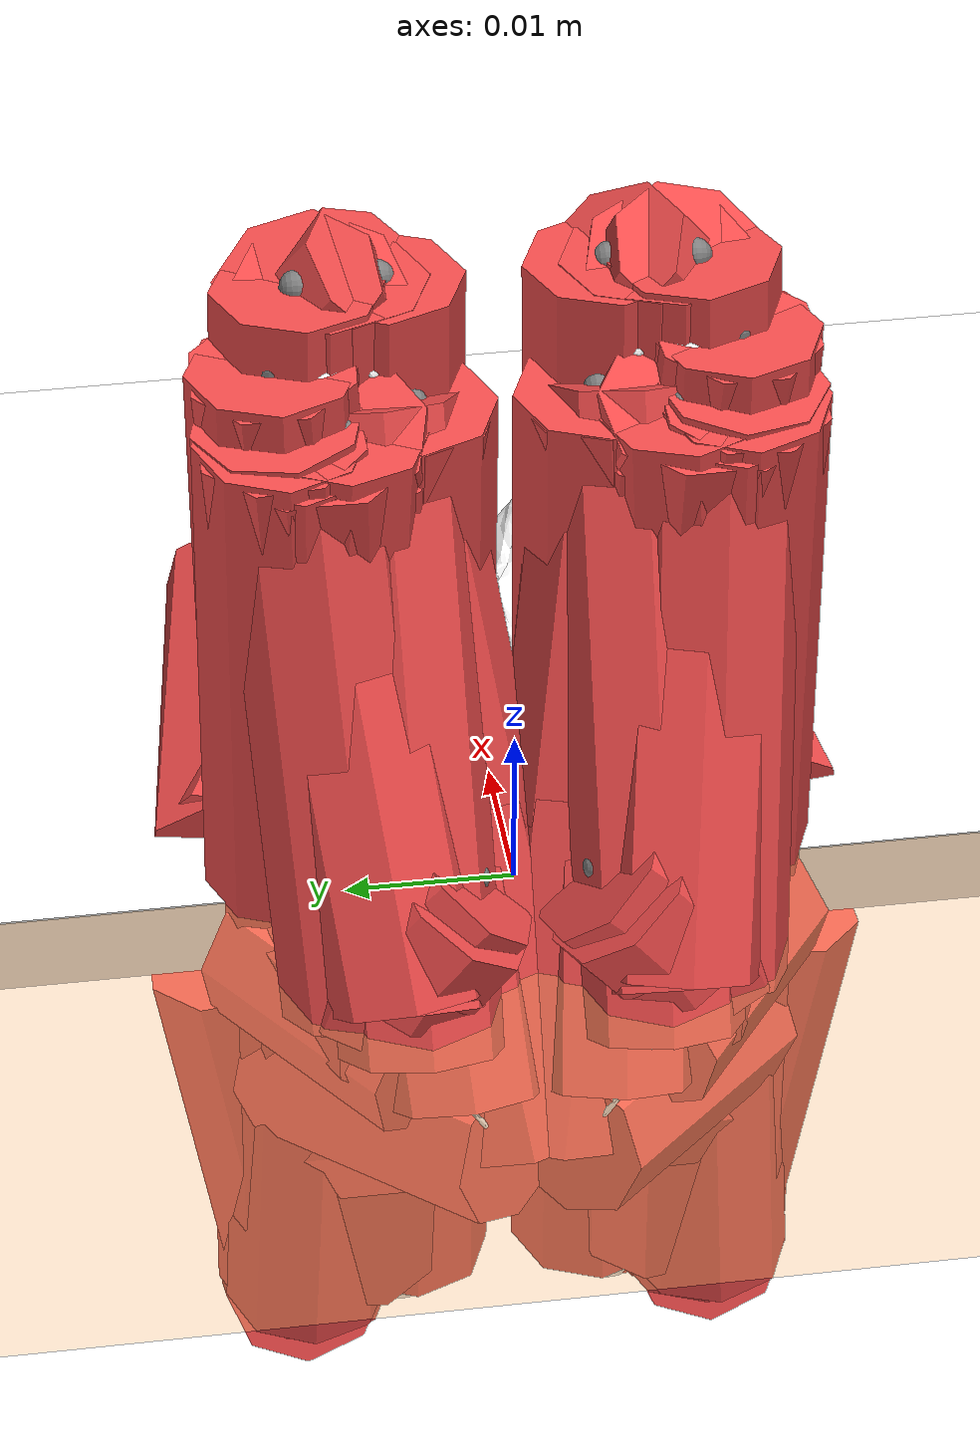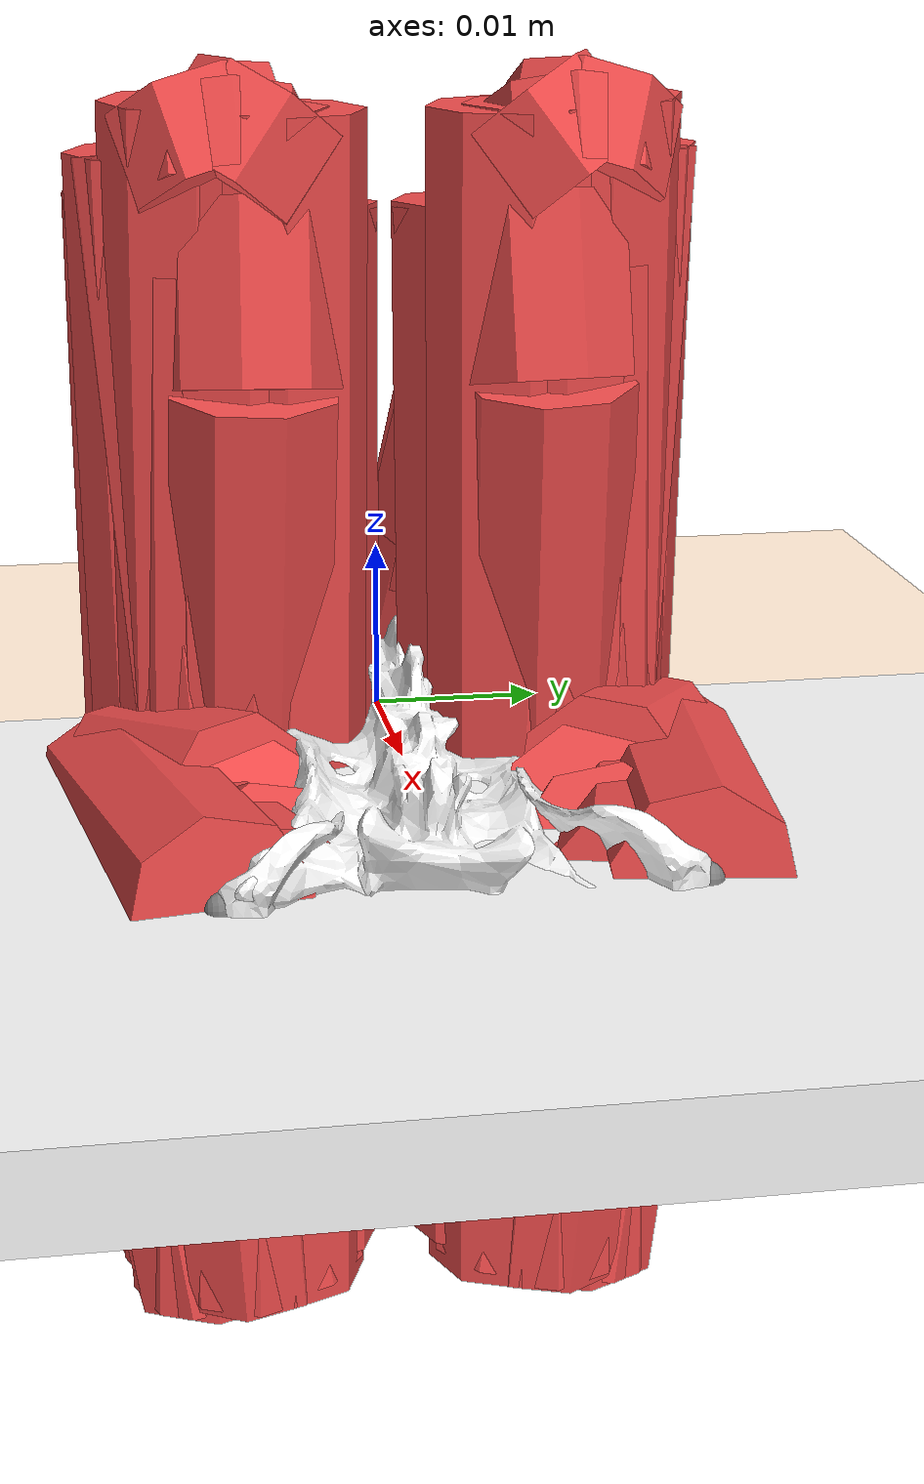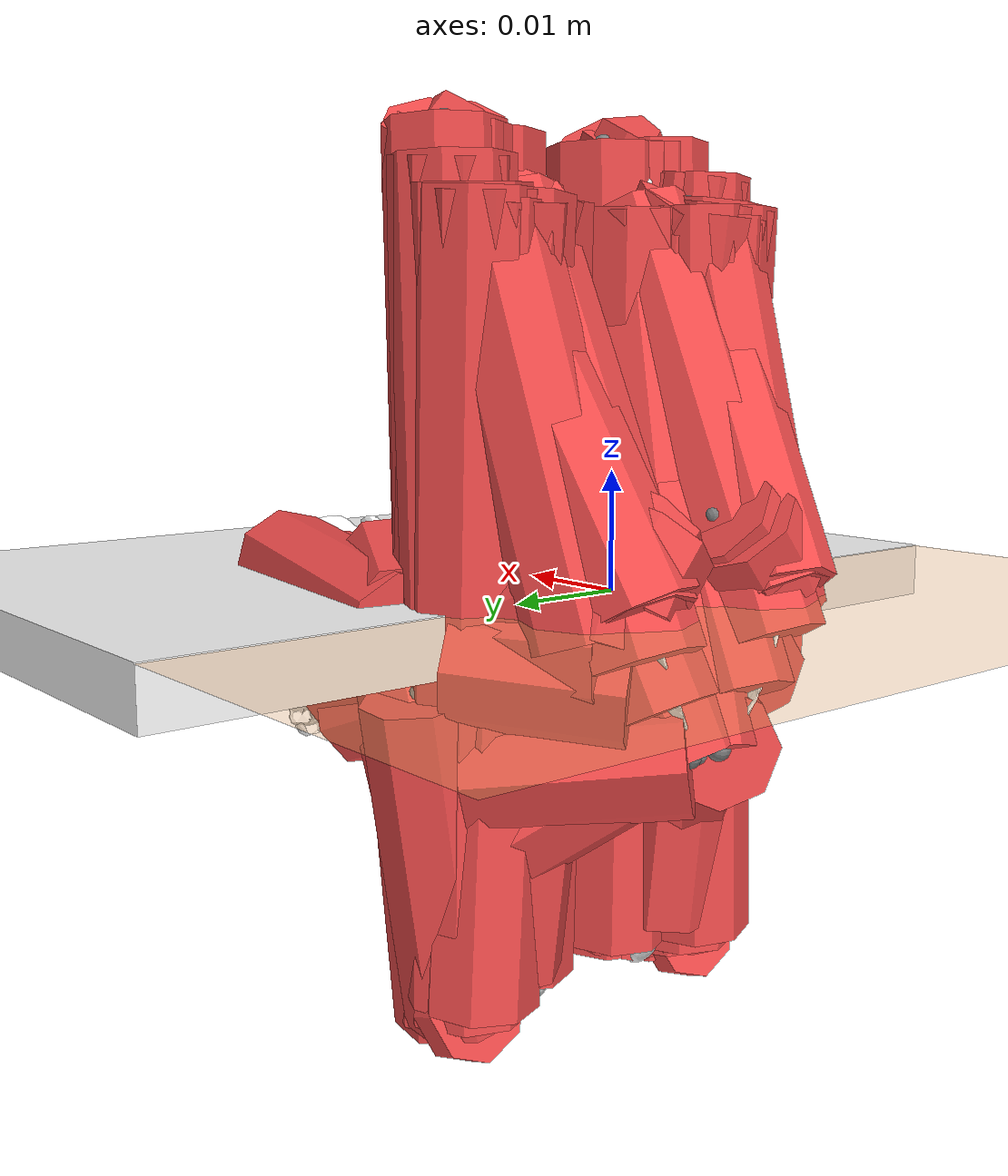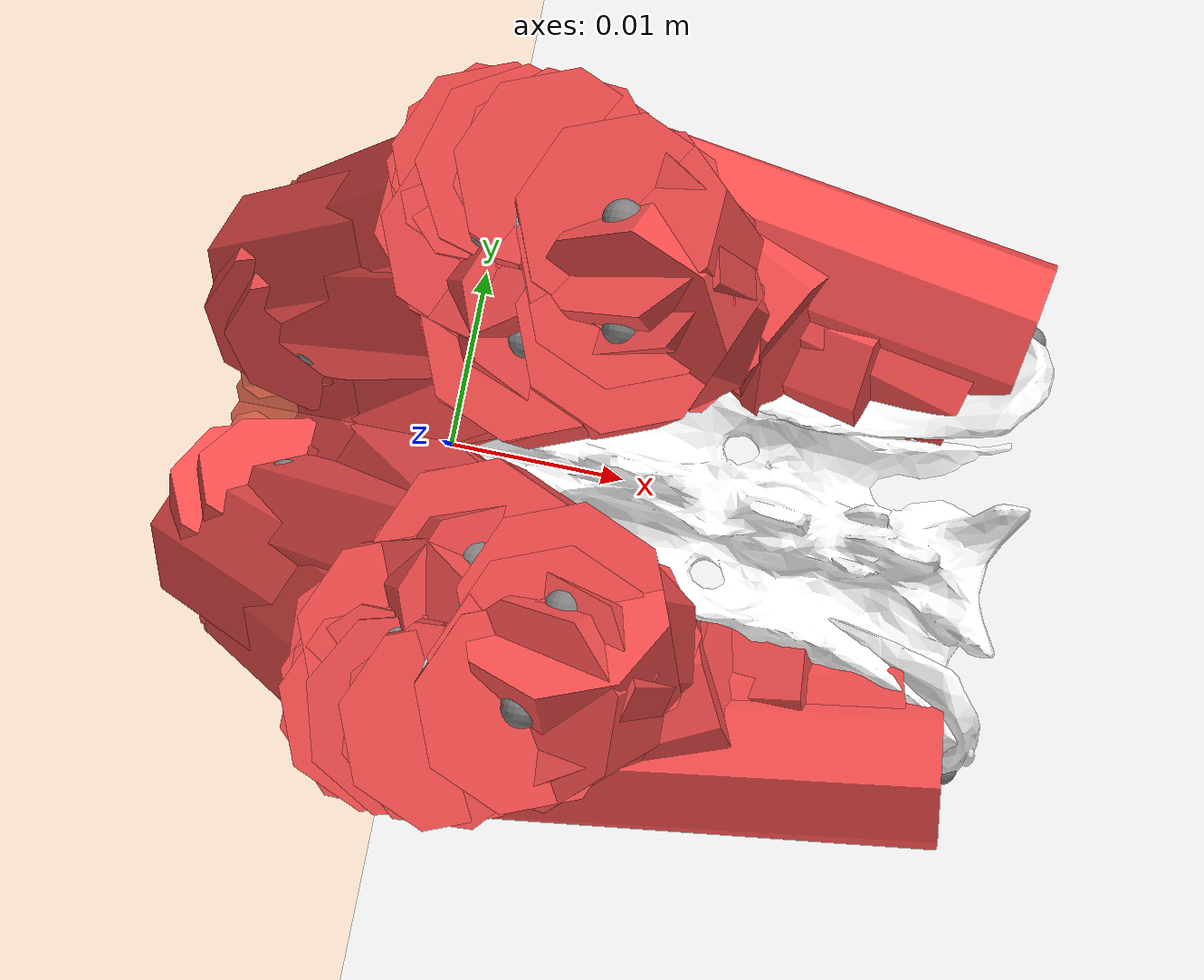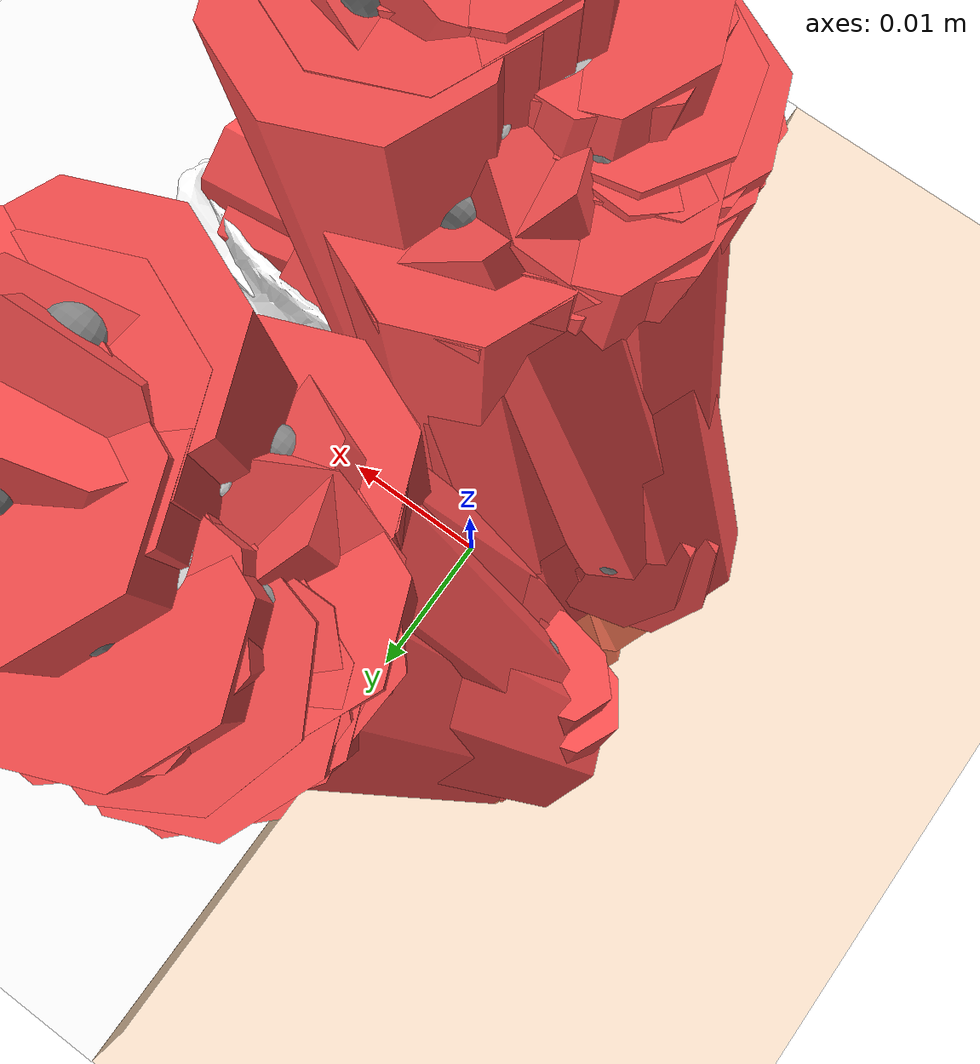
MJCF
<mujoco model="template">
  <!-- This model has been converted from an OpenSim model. Model conversion by MyoConverter https://github.com/MyoHub/myoconverter. This model is licensed under Apache 2.0. -->
  <compiler angle="radian" autolimits="true"/>
  <size njmax="1000" nconmax="400" nkey="1" nuser_jnt="1"/>
  <visual>
    <scale framelength="0.5" framewidth="0.01"/>
  </visual>
  <statistic meansize="0.0403277" extent="2" center="0 0 0"/>
  <default class="main">
    <joint limited="true" armature="1e-05" damping="0.05"/>
    <geom margin="0.001" rgba="0.8 0.6 0.4 1"/>
    <site size="0.001 0.005 0.005"/>
    <tendon limited="false" width="0.005" rgba="0.95 0.3 0.3 1"/>
    <default class="muscle">
      <general ctrllimited="true" ctrlrange="0 1" dyntype="muscle" gaintype="muscle" biastype="muscle" dynprm="0.01 0.04 0 0 0 0 0 0 0 0" gainprm="0.75 1.05 -1 200 0.5 1.6 1.5 1.3 1.2 0" biasprm="0.75 1.05 -1 200 0.5 1.6 1.5 1.3 1.2 0"/>
    </default>
    <default class="motor">
      <general gainprm="5 0 0 0 0 0 0 0 0 0"/>
    </default>
  </default>
  <asset>
    <texture type="skybox" builtin="gradient" rgb1="1 1 1" rgb2="0.6 0.8 1" width="256" height="1536"/>
    <mesh name="ground_geom_1_ground" file="Geometry/ground.stl"/>
    <mesh name="spine_geom_1_spine_y2j" file="Geometry/spine_y2j.stl"/>
    <mesh name="pelvis_r_geom_1_pelvis_r_y2j" file="Geometry/pelvis_r_y2j.stl"/>
    <mesh name="femur_r_geom_1_femur_r_y2j" file="Geometry/femur_r_y2j.stl"/>
    <mesh name="tibia_r_geom_1_tibia_r_y2j" file="Geometry/tibia_r_y2j.stl"/>
    <mesh name="foot_r_geom_1_foot_r_y2j" file="Geometry/foot_r_y2j.stl"/>
    <mesh name="pelvis_l_geom_1_pelvis_r_y2j" file="Geometry/pelvis_r_y2j.stl" scale="1 1 -1"/>
    <mesh name="femur_l_geom_1_femur_r_y2j" file="Geometry/femur_r_y2j.stl" scale="1 1 -1"/>
    <mesh name="tibia_l_geom_1_tibia_r_y2j" file="Geometry/tibia_r_y2j.stl" scale="1 1 -1"/>
    <mesh name="foot_l_geom_1_foot_r_y2j" file="Geometry/foot_r_y2j.stl" scale="1 1 -1"/>
  </asset>
  <worldbody>
    <light pos="0 0 0" dir="0 0 -1" directional="true"/>
    <body name="ground" quat="0.707035 0.707179 0 0">
      <geom name="ground-plane" size="10 10 0.125" quat="0.707035 -0.707179 0 0" type="plane" rgba="1 0.7 0.4 1"/>
      <geom name="ground_geom_1" type="mesh" rgba="1 1 1 1" mesh="ground_geom_1_ground"/>
    </body>
    <body name="spine" quat="0.707035 0.707179 0 0">
      <inertial pos="0 0 0" mass="0.12" diaginertia="0.001 0.001 0.001"/>
      <joint name="sacrum_x" pos="0 0 0" axis="1 0 0" type="slide" range="-0.1 0.25" damping="0"/>
      <joint name="sacrum_y" pos="0 0 0" axis="0 1 0" type="slide" range="0 0.2" damping="0" user="0.05"/>
      <joint name="sacrum_z" pos="0 0 0" axis="0 0 1" type="slide" range="-0.1 0.1" damping="0"/>
      <joint name="sacrum_pitch" pos="0 0 0" axis="0 0 1" range="-1.571 1.571" damping="0" user="0.523599"/>
      <joint name="sacrum_roll" pos="0 0 0" axis="1 0 0" range="-1.571 1.571" damping="0"/>
      <joint name="sacrum_yaw" pos="0 0 0" axis="0 1 0" range="-1.571 1.571" damping="0"/>
      <geom name="spine_geom_1" type="mesh" rgba="1 1 1 1" mesh="spine_geom_1_spine_y2j"/>
      <body name="pelvis_r" pos="0.005 -0.003 0.01">
        <inertial pos="0 0 0" mass="0.02" diaginertia="0.001 0.001 0.001"/>
        <joint name="sacroiliac_r_flx" pos="0 0 0" axis="0 0 1" range="-0.02301 0.1515" user="0.0645772"/>
        <geom name="pelvis_r_geom_1" type="mesh" rgba="1 1 1 1" mesh="pelvis_r_geom_1_pelvis_r_y2j"/>
        <site name="R_BFa_R_BFa_pelvis_r_origin_1" pos="-0.0132297 0.00980549 -0.0063166"/>
        <site name="R_BFa_R_BFa_pelvis_r_via_2" pos="-0.0133788 0.00534739 -0.00170754"/>
        <site name="R_BFa_R_BFa_pelvis_r_via_3" pos="-0.0134136 0.0012675 -0.000195299"/>
        <site name="R_BFp_R_BFp_pelvis_r_origin_1" pos="-0.0161622 0.00370234 -0.00225771"/>
        <site name="R_CF_R_CF_pelvis_r_origin_1" pos="-0.00767728 0.0100753 -0.00608851"/>
        <site name="R_CF_R_CF_pelvis_r_via_2" pos="-0.00711651 0.00552975 -0.00273974"/>
        <site name="R_CF_R_CF_pelvis_r_via_3" pos="-0.00599402 0.00120374 -0.00112437"/>
        <site name="R_STp_R_STp_pelvis_r_origin_1" pos="-0.015921 0.00265139 -0.00235452"/>
        <site name="R_STa_R_STa_pelvis_r_origin_1" pos="-0.0146708 0.00908058 -0.00542682"/>
        <site name="R_STa_R_STa_pelvis_r_via_2" pos="-0.0146566 0.00599214 -0.00289419"/>
        <site name="R_STa_R_STa_pelvis_r_via_3" pos="-0.0146655 0.00390982 -0.00173483"/>
        <site name="R_SM_R_SM_pelvis_r_origin_1" pos="-0.0159234 -0.000401862 -0.00310496"/>
        <site name="R_QF_R_QF_pelvis_r_origin_1" pos="-0.0143109 -0.00272027 -0.00387669"/>
        <site name="R_TFL_R_TFL_pelvis_r_origin_1" pos="0.0164981 0.00094155 -0.00148761"/>
        <site name="R_GMa_R_GMa_pelvis_r_origin_1" pos="0.0144019 0.00283364 -0.00103718"/>
        <site name="R_GMe_R_GMe_pelvis_r_origin_1" pos="0.0262291 0.00298272 0.00243583"/>
        <site name="R_GMi_R_GMi_pelvis_r_origin_1" pos="0.0236967 0.00135748 -0.000410322"/>
        <site name="R_Pir_R_Pir_pelvis_r_origin_1" pos="0.0128648 0.00361072 4.01502e-05"/>
        <site name="R_GP_R_GP_pelvis_r_origin_1" pos="-0.0150306 -0.00490004 -0.00569407"/>
        <site name="R_GA_R_GA_pelvis_r_origin_1" pos="-0.0143754 -0.00903598 -0.00926684"/>
        <site name="R_AL_R_AL_pelvis_r_origin_1" pos="-0.00492821 -0.00590076 -0.00619486"/>
        <site name="R_AM_R_AM_pelvis_r_origin_1" pos="-0.0130209 -0.00907341 -0.00926436"/>
        <site name="R_AB_R_AB_pelvis_r_origin_1" pos="-0.0124209 -0.00798705 -0.00854123"/>
        <site name="R_Pec_R_Pec_pelvis_r_origin_1" pos="-0.0158755 -0.00847373 -0.00832466"/>
        <site name="R_IP_R_IP_pelvis_r_origin_1" pos="0.0217579 -0.0010771 -0.00213784"/>
        <site name="R_OE_R_OE_pelvis_r_origin_1" pos="-0.00977741 -0.00174751 -0.00349642"/>
        <site name="R_OI_R_OI_pelvis_r_origin_1" pos="-0.0137743 -0.00025582 -0.00241615"/>
        <site name="R_GS_R_GS_pelvis_r_origin_1" pos="0.019057 0.00184775 -0.00103652"/>
        <site name="R_GI_R_GI_pelvis_r_origin_1" pos="-0.0124186 0.00572197 -0.00298061"/>
        <site name="R_RF_R_RF_pelvis_r_origin_1" pos="0.00479528 -0.000432256 0.00134144"/>
        <site name="R_Iliac_Crest_marker" pos="0.028 0.004 0.01" size="0.01" group="4" rgba="1 0.1 0.5 0.5"/>
        <site name="R_Hip_marker" pos="-0.005 0.005 0.01" size="0.01" group="4" rgba="1 0.1 0.5 0.5"/>
        <body name="femur_r">
          <inertial pos="0 -0.015 0" quat="0.707107 0.707107 0 0" mass="0.02" diaginertia="0.001 0.001 0.001"/>
          <joint name="hip_r_flx" pos="0 0 0" axis="0 0 1" range="-0.8727 1.222" user="0.698132"/>
          <joint name="hip_r_add" pos="0 0 0" axis="1 0 0" range="-0.8727 0.3491" user="-0.174533"/>
          <joint name="hip_r_int" pos="0 0 0" axis="0 1 0" range="-0.8727 0.6981"/>
          <geom name="femur_r_geom_1" type="mesh" rgba="1 1 1 1" mesh="femur_r_geom_1_femur_r_y2j"/>
          <site name="R_CF_R_CF_femur_r_insertion_4" pos="-0.00226843 -0.0279103 -0.000618424"/>
          <site name="R_QF_R_QF_femur_r_insertion_2" pos="-0.00313572 -0.00154175 0.00490289"/>
          <site name="R_TFL_R_TFL_femur_r_insertion_2" pos="0.0011165 -0.0206029 0.00213452"/>
          <site name="R_GMa_R_GMa_femur_r_insertion_2" pos="-0.00131757 -0.00888287 0.00582157"/>
          <site name="R_GMe_R_GMe_femur_r_insertion_2" pos="0.00123694 0.000620532 0.00639234"/>
          <site name="R_GMi_R_GMi_femur_r_insertion_2" pos="0.00135415 -0.000395314 0.00570301"/>
          <site name="R_Pir_R_Pir_femur_r_insertion_2" pos="0.00177067 0.00124939 0.00576703"/>
          <site name="R_AL_R_AL_femur_r_insertion_2" pos="-0.00199182 -0.0153779 0.00151891"/>
          <site name="R_AB_R_AB_femur_r_insertion_2" pos="-0.0020575 -0.0173788 0.00193487"/>
          <site name="R_Pec_R_Pec_femur_r_insertion_2" pos="-0.00312683 -0.0105314 0.00347823"/>
          <site name="R_IP_R_IP_femur_r_insertion_2" pos="-0.000256598 -0.00442203 0.00160047"/>
          <site name="R_OE_R_OE_femur_r_insertion_2" pos="-0.00194615 -0.00151547 0.00167137"/>
          <site name="R_OI_R_OI_femur_r_via_2" pos="-0.000955125 -0.00018124 0.00329424"/>
          <site name="R_GS_R_GS_femur_r_insertion_2" pos="-3.50381e-05 -0.00636066 0.00236695"/>
          <site name="R_GI_R_GI_femur_r_insertion_2" pos="-0.00180094 -0.000409483 0.00195963"/>
          <site name="R_RF_R_RF_femur_r_via_2" pos="0.00306846 -0.0319159 -0.000690338"/>
          <site name="R_VL_R_VL_femur_r_origin_1" pos="-0.00127121 -0.00399329 0.00678054"/>
          <site name="R_VL_R_VL_femur_r_via_2" pos="-0.00044582 -0.0320663 0.0020791"/>
          <site name="R_VI_R_VI_femur_r_origin_1" pos="-0.000455439 -0.0103898 0.0050255"/>
          <site name="R_VI_R_VI_femur_r_via_2" pos="0.00159478 -0.0330209 0.00171735"/>
          <site name="R_VM_R_VM_femur_r_origin_1" pos="-0.000252952 -0.00533152 0.00171168"/>
          <site name="R_VM_R_VM_femur_r_via_2" pos="0.00232742 -0.0319002 -0.00288875"/>
          <site name="R_MG_R_MG_femur_r_origin_1" pos="0.000388787 -0.0303357 -0.00417502"/>
          <site name="R_LG_R_LG_femur_r_origin_1" pos="-0.00153153 -0.0297815 0.00297271"/>
          <site name="R_Pla_R_Pla_femur_r_origin_1" pos="-0.00149972 -0.0289394 0.00235859"/>
          <site name="R_EDL_R_EDL_femur_r_origin_1" pos="-0.00175163 -0.0314643 0.00217994"/>
          <site name="R_Pop_R_Pop_femur_r_origin_1" pos="-0.00101877 -0.0308136 0.0027711"/>
          <site name="R_Pop_R_Pop_femur_r_via_2" pos="-0.00322079 -0.0300782 0.00270043"/>
          <site name="R_Knee_marker" pos="0 -0.035 0" size="0.01" group="4" rgba="1 0.1 0.5 0.5"/>
          <body name="tibia_r">
            <inertial pos="0 0.015 0" quat="0.707107 0.707107 0 0" mass="0.02" diaginertia="0.001 0.001 0.001"/>
            <joint name="knee_r_translation1" pos="0 0 0" axis="1 0 0" type="slide" range="-0.04232 -0.01539" user="-0.0379833"/>
            <joint name="knee_r_translation2" pos="0 0 0" axis="0 1 0" type="slide" range="-0.0695 0.00082" user="-0.0135276"/>
            <joint name="knee_r_translation3" pos="0 0 0" axis="0 0 1" type="slide" range="-0.00371 0.00227" user="0.00116828"/>
            <joint name="knee_r_flx" pos="0 0 0" axis="0 0 1" range="-2.618 -0.3491" user="-2.0944"/>
            <joint name="knee_r_rotation2" pos="0 0 0" axis="1 0 0" range="-0.08727 0.06458" user="-0.0523844"/>
            <joint name="knee_r_rotation3" pos="0 0 0" axis="0 1 0" limited="false" range="-2.618 -0.3491" user="-2.0944"/>
            <geom name="tibia_r_geom_1" type="mesh" rgba="1 1 1 1" mesh="tibia_r_geom_1_tibia_r_y2j"/>
            <site name="R_BFa_R_BFa_tibia_r_insertion_4" pos="-0.00348453 0.0320117 0.00152993"/>
            <site name="R_BFp_R_BFp_tibia_r_via_2" pos="-0.00365577 0.0262903 0.000579411"/>
            <site name="R_BFp_R_BFp_tibia_r_insertion_3" pos="0.00203029 0.0268989 0.000128784"/>
            <site name="R_STp_R_STp_tibia_r_insertion_2" pos="0.00195451 0.0271586 -0.00220043"/>
            <site name="R_STa_R_STa_tibia_r_insertion_4" pos="0.00195451 0.0271586 -0.00220043"/>
            <site name="R_SM_R_SM_tibia_r_insertion_2" pos="0.000134283 0.0340678 -0.00267487"/>
            <site name="R_GP_R_GP_tibia_r_insertion_2" pos="0.00191208 0.0280449 -0.00294073"/>
            <site name="R_GA_R_GA_tibia_r_insertion_2" pos="0.00134625 0.0305425 -0.00288332"/>
            <site name="R_AM_R_AM_tibia_r_insertion_2" pos="0.000597057 0.0322462 -0.00276148"/>
            <site name="R_RF_R_RF_tibia_r_via_3" pos="0.00323906 0.0400816 -0.00138431"/>
            <site name="R_VL_R_VL_tibia_r_via_3" pos="0.0024724 0.040377 0.001254"/>
            <site name="R_VL_R_VL_tibia_r_insertion_4" pos="0.00471886 0.0356258 -0.000219232"/>
            <site name="R_VI_R_VI_tibia_r_via_3" pos="0.00275953 0.0400933 -8.17198e-05"/>
            <site name="R_VI_R_VI_tibia_r_insertion_4" pos="0.00471886 0.0356258 -0.000219232"/>
            <site name="R_VM_R_VM_tibia_r_via_3" pos="0.00342083 0.0399824 -0.00342434"/>
            <site name="R_VM_R_VM_tibia_r_insertion_4" pos="0.00471886 0.0356258 -0.000219232"/>
            <site name="R_MG_R_MG_tibia_r_via_2" pos="-0.00106955 0.0343249 -0.00460699"/>
            <site name="R_MG_R_MG_tibia_r_via_3" pos="-0.00017209 -7.22075e-05 -0.00227131"/>
            <site name="R_LG_R_LG_tibia_r_via_2" pos="-0.00405851 0.0347773 0.0030712"/>
            <site name="R_LG_R_LG_tibia_r_via_3" pos="-0.00054475 0.000622435 0.000711555"/>
            <site name="R_Pla_R_Pla_tibia_r_via_2" pos="-0.00421592 0.0339425 0.00230871"/>
            <site name="R_Pla_R_Pla_tibia_r_via_3" pos="-0.000522006 0.000624534 0.000288951"/>
            <site name="R_Sol_R_Sol_tibia_r_origin_1" pos="-0.00442459 0.0340242 0.000539192"/>
            <site name="R_Sol_R_Sol_tibia_r_via_2" pos="-0.000487865 0.000627685 -0.000345418"/>
            <site name="R_TA_R_TA_tibia_r_origin_1" pos="0.00355054 0.0350377 -0.00194405"/>
            <site name="R_TA_R_TA_tibia_r_via_2" pos="0.00564702 0.0250468 -0.00170573"/>
            <site name="R_TA_R_TA_tibia_r_via_3" pos="0.0027597 0.00233773 -0.00133212"/>
            <site name="R_EDL_R_EDL_tibia_r_via_2" pos="-0.000921634 0.0373975 0.00307325"/>
            <site name="R_EDL_R_EDL_tibia_r_via_3" pos="0.00252069 0.00212708 0.000566363"/>
            <site name="R_TP_R_TP_tibia_r_origin_1" pos="-0.00233454 0.0322364 -0.00145404"/>
            <site name="R_TP_R_TP_tibia_r_via_2" pos="-0.000282222 6.85887e-05 -0.00162168"/>
            <site name="R_FDL_R_FDL_tibia_r_origin_1" pos="-0.00268406 0.0340952 -0.000786405"/>
            <site name="R_FDL_R_FDL_tibia_r_via_2" pos="-0.000170871 0.000537963 -0.00122305"/>
            <site name="R_FHL_R_FHL_tibia_r_origin_1" pos="-0.00106867 0.0320068 -0.00138705"/>
            <site name="R_FHL_R_FHL_tibia_r_via_2" pos="-0.000271605 0.000384977 -0.00199028"/>
            <site name="R_Per_R_Per_tibia_r_origin_1" pos="-0.00284586 0.0352601 0.00311464"/>
            <site name="R_Per_R_Per_tibia_r_via_2" pos="-0.000565344 0.000620534 0.00109422"/>
            <site name="R_Pop_R_Pop_tibia_r_via_3" pos="-0.00386284 0.0346011 -0.000335933"/>
            <site name="R_Pop_R_Pop_tibia_r_insertion_4" pos="0.00189179 0.0251465 -0.00236471"/>
            <site name="R_Ankle_marker" pos="0 0 0.004" size="0.01" group="4" rgba="1 0.1 0.5 0.5"/>
            <body name="foot_r">
              <inertial pos="0.007 -0.005 0" quat="0.5 0.5 0.5 0.5" mass="0.02" diaginertia="0.001 0.001 0.001"/>
              <joint name="ankle_r_translation1" pos="0 0 0" axis="1 0 0" type="slide" range="-1e-06 0"/>
              <joint name="ankle_r_translation2" pos="0 0 0" axis="0 1 0" type="slide" range="-1e-06 0"/>
              <joint name="ankle_r_translation3" pos="0 0 0" axis="0 0 1" type="slide" range="-1e-06 0"/>
              <joint name="ankle_r_flx" pos="0 0 0" axis="0 0 1" range="-0.5236 1.047" user="0.872665"/>
              <joint name="ankle_r_add" pos="0 0 0" axis="1 0 0" range="-0.08727 0.6109" user="-0.0872665"/>
              <joint name="ankle_r_int" pos="0 0 0" axis="0 1 0" range="-0.8727 0.2618"/>
              <geom name="foot_r_geom_1" type="mesh" rgba="1 1 1 1" mesh="foot_r_geom_1_foot_r_y2j"/>
              <site name="R_MG_R_MG_foot_r_via_4" pos="-0.00262931 -0.000720471 -0.000656838"/>
              <site name="R_MG_R_MG_foot_r_insertion_5" pos="-0.00258174 -0.00187843 -0.000213927"/>
              <site name="R_LG_R_LG_foot_r_via_4" pos="-0.00332118 -0.000750235 0.000807188"/>
              <site name="R_LG_R_LG_foot_r_insertion_5" pos="-0.00264158 -0.00183517 0.000842338"/>
              <site name="R_Pla_R_Pla_foot_r_via_4" pos="-0.00327974 -0.000757689 0.000376657"/>
              <site name="R_Pla_R_Pla_foot_r_insertion_5" pos="-0.00299362 -0.00196071 0.000233615"/>
              <site name="R_Sol_R_Sol_foot_r_via_3" pos="-0.0032181 -0.000769981 3.92458e-05"/>
              <site name="R_Sol_R_Sol_foot_r_insertion_4" pos="-0.00294726 -0.00193395 -0.000110474"/>
              <site name="R_TA_R_TA_foot_r_via_4" pos="0.00421949 -0.00166742 -0.000420508"/>
              <site name="R_TA_R_TA_foot_r_insertion_5" pos="0.00659687 -0.00358719 -0.000940153"/>
              <site name="R_EDL_R_EDL_foot_r_via_4" pos="0.00361668 -0.00182047 0.00134594"/>
              <site name="R_EDL_R_EDL_foot_r_insertion_5" pos="0.0161795 -0.00737943 0.00241444"/>
              <site name="R_TP_R_TP_foot_r_via_3" pos="-0.00334001 -0.000789046 -0.000600014"/>
              <site name="R_TP_R_TP_foot_r_via_4" pos="-0.00101312 -0.00262057 -0.000359079"/>
              <site name="R_TP_R_TP_foot_r_insertion_5" pos="0.00346681 -0.00392925 -0.00124231"/>
              <site name="R_FDL_R_FDL_foot_r_via_3" pos="-0.00323618 -0.000760907 -0.000349193"/>
              <site name="R_FDL_R_FDL_foot_r_via_4" pos="-0.00126024 -0.00233229 -0.000125008"/>
              <site name="R_FDL_R_FDL_foot_r_via_5" pos="0.001478 -0.00391883 -0.000336048"/>
              <site name="R_FDL_R_FDL_foot_r_insertion_6" pos="0.0147301 -0.00907332 0.00227709"/>
              <site name="R_FHL_R_FHL_foot_r_via_3" pos="-0.00294651 -0.000900305 -0.000693831"/>
              <site name="R_FHL_R_FHL_foot_r_via_4" pos="-0.00093843 -0.0025362 -0.000802729"/>
              <site name="R_FHL_R_FHL_foot_r_via_5" pos="0.00221994 -0.00406605 -0.000505777"/>
              <site name="R_FHL_R_FHL_foot_r_insertion_6" pos="0.0150406 -0.00868818 -0.000491204"/>
              <site name="R_Per_R_Per_foot_r_via_3" pos="-0.00295525 -0.000837963 0.001232"/>
              <site name="R_Per_R_Per_foot_r_via_4" pos="-0.000810172 -0.00246752 0.0015154"/>
              <site name="R_Per_R_Per_foot_r_via_5" pos="0.00151295 -0.00391838 0.00188985"/>
              <site name="R_Per_R_Per_foot_r_insertion_6" pos="0.00448748 -0.00505317 0.000872061"/>
              <site name="R_Toe_marker" pos="0.015 -0.005 0.005" size="0.01" group="4" rgba="1 0.1 0.5 0.5"/>
            </body>
          </body>
        </body>
      </body>
      <body name="pelvis_l" pos="0.005 -0.003 -0.01">
        <inertial pos="0 0 0" mass="0.02" diaginertia="0.001 0.001 0.001"/>
        <joint name="sacroiliac_l_flx" pos="0 0 0" axis="0 0 1" range="-0.02301 0.1515" user="0.0645772"/>
        <geom name="pelvis_l_geom_1" type="mesh" rgba="1 1 1 1" mesh="pelvis_l_geom_1_pelvis_r_y2j"/>
        <site name="L_BFa_L_BFa_pelvis_l_origin_1" pos="-0.0132297 0.00980549 0.0063166"/>
        <site name="L_BFa_L_BFa_pelvis_l_via_2" pos="-0.0133788 0.00534739 0.00170754"/>
        <site name="L_BFa_L_BFa_pelvis_l_via_3" pos="-0.0134136 0.0012675 0.000195299"/>
        <site name="L_BFp_L_BFp_pelvis_l_origin_1" pos="-0.0161622 0.00370234 0.00225771"/>
        <site name="L_CF_L_CF_pelvis_l_origin_1" pos="-0.00767728 0.0100753 0.00608851"/>
        <site name="L_CF_L_CF_pelvis_l_via_2" pos="-0.00711651 0.00552975 0.00273974"/>
        <site name="L_CF_L_CF_pelvis_l_via_3" pos="-0.00599402 0.00120374 0.00112437"/>
        <site name="L_STp_L_STp_pelvis_l_origin_1" pos="-0.015921 0.00265139 0.00235452"/>
        <site name="L_STa_L_STa_pelvis_l_origin_1" pos="-0.0146708 0.00908058 0.00542682"/>
        <site name="L_STa_L_STa_pelvis_l_via_2" pos="-0.0146566 0.00599214 0.00289419"/>
        <site name="L_STa_L_STa_pelvis_l_via_3" pos="-0.0146655 0.00390982 0.00173483"/>
        <site name="L_SM_L_SM_pelvis_l_origin_1" pos="-0.0159234 -0.000401862 0.00310496"/>
        <site name="L_QF_L_QF_pelvis_l_origin_1" pos="-0.0143109 -0.00272027 0.00387669"/>
        <site name="L_TFL_L_TFL_pelvis_l_origin_1" pos="0.0164981 0.00094155 0.00148761"/>
        <site name="L_GMa_L_GMa_pelvis_l_origin_1" pos="0.0144019 0.00283364 0.00103718"/>
        <site name="L_GMe_L_GMe_pelvis_l_origin_1" pos="0.0262291 0.00298272 -0.00243583"/>
        <site name="L_GMi_L_GMi_pelvis_l_origin_1" pos="0.0236967 0.00135748 0.000410322"/>
        <site name="L_Pir_L_Pir_pelvis_l_origin_1" pos="0.0128648 0.00361072 -4.01502e-05"/>
        <site name="L_GP_L_GP_pelvis_l_origin_1" pos="-0.0150306 -0.00490004 0.00569407"/>
        <site name="L_GA_L_GA_pelvis_l_origin_1" pos="-0.0143754 -0.00903598 0.00926684"/>
        <site name="L_AL_L_AL_pelvis_l_origin_1" pos="-0.00492821 -0.00590076 0.00619486"/>
        <site name="L_AM_L_AM_pelvis_l_origin_1" pos="-0.0130209 -0.00907341 0.00926436"/>
        <site name="L_AB_L_AB_pelvis_l_origin_1" pos="-0.0124209 -0.00798705 0.00854123"/>
        <site name="L_Pec_L_Pec_pelvis_l_origin_1" pos="-0.0158755 -0.00847373 0.00832466"/>
        <site name="L_IP_L_IP_pelvis_l_origin_1" pos="0.0217579 -0.0010771 0.00213784"/>
        <site name="L_OE_L_OE_pelvis_l_origin_1" pos="-0.00977741 -0.00174751 0.00349642"/>
        <site name="L_OI_L_OI_pelvis_l_origin_1" pos="-0.0137743 -0.00025582 0.00241615"/>
        <site name="L_GS_L_GS_pelvis_l_origin_1" pos="0.019057 0.00184775 0.00103652"/>
        <site name="L_GI_L_GI_pelvis_l_origin_1" pos="-0.0124186 0.00572197 0.00298061"/>
        <site name="L_RF_L_RF_pelvis_l_origin_1" pos="0.00479528 -0.000432256 -0.00134144"/>
        <body name="femur_l">
          <inertial pos="0 -0.015 0" quat="0.707107 0.707107 0 0" mass="0.02" diaginertia="0.001 0.001 0.001"/>
          <joint name="hip_l_flx" pos="0 0 0" axis="0 0 1" range="-0.8727 1.222" user="0.698132"/>
          <joint name="hip_l_add" pos="0 0 0" axis="-1 0 0" range="-0.8727 0.3491" user="0.174533"/>
          <joint name="hip_l_int" pos="0 0 0" axis="0 -1 0" range="-0.8727 0.6981"/>
          <geom name="femur_l_geom_1" type="mesh" rgba="1 1 1 1" mesh="femur_l_geom_1_femur_r_y2j"/>
          <site name="L_CF_L_CF_femur_l_insertion_4" pos="-0.00226843 -0.0279103 0.000618424"/>
          <site name="L_QF_L_QF_femur_l_insertion_2" pos="-0.00313572 -0.00154175 -0.00490289"/>
          <site name="L_TFL_L_TFL_femur_l_insertion_2" pos="0.0011165 -0.0206029 -0.00213452"/>
          <site name="L_GMa_L_GMa_femur_l_insertion_2" pos="-0.00131757 -0.00888287 -0.00582157"/>
          <site name="L_GMe_L_GMe_femur_l_insertion_2" pos="0.00123694 0.000620532 -0.00639234"/>
          <site name="L_GMi_L_GMi_femur_l_insertion_2" pos="0.00135415 -0.000395314 -0.00570301"/>
          <site name="L_Pir_L_Pir_femur_l_insertion_2" pos="0.00177067 0.00124939 -0.00576703"/>
          <site name="L_AL_L_AL_femur_l_insertion_2" pos="-0.00199182 -0.0153779 -0.00151891"/>
          <site name="L_AB_L_AB_femur_l_insertion_2" pos="-0.0020575 -0.0173788 -0.00193487"/>
          <site name="L_Pec_L_Pec_femur_l_insertion_2" pos="-0.00312683 -0.0105314 -0.00347823"/>
          <site name="L_IP_L_IP_femur_l_insertion_2" pos="-0.000256598 -0.00442203 -0.00160047"/>
          <site name="L_OE_L_OE_femur_l_insertion_2" pos="-0.00194615 -0.00151547 -0.00167137"/>
          <site name="L_OI_L_OI_femur_l_via_2" pos="-0.000955125 -0.00018124 -0.00329424"/>
          <site name="L_GS_L_GS_femur_l_insertion_2" pos="-3.50381e-05 -0.00636066 -0.00236695"/>
          <site name="L_GI_L_GI_femur_l_insertion_2" pos="-0.00180094 -0.000409483 -0.00195963"/>
          <site name="L_RF_L_RF_femur_l_via_2" pos="0.00306846 -0.0319159 0.000690338"/>
          <site name="L_VL_L_VL_femur_l_origin_1" pos="-0.00127121 -0.00399329 -0.00678054"/>
          <site name="L_VL_L_VL_femur_l_via_2" pos="-0.00044582 -0.0320663 -0.0020791"/>
          <site name="L_VI_L_VI_femur_l_origin_1" pos="-0.000455439 -0.0103898 -0.0050255"/>
          <site name="L_VI_L_VI_femur_l_via_2" pos="0.00159478 -0.0330209 -0.00171735"/>
          <site name="L_VM_L_VM_femur_l_origin_1" pos="-0.000252952 -0.00533152 -0.00171168"/>
          <site name="L_VM_L_VM_femur_l_via_2" pos="0.00232742 -0.0319002 0.00288875"/>
          <site name="L_MG_L_MG_femur_l_origin_1" pos="0.000388787 -0.0303357 0.00417502"/>
          <site name="L_LG_L_LG_femur_l_origin_1" pos="-0.00153153 -0.0297815 -0.00297271"/>
          <site name="L_Pla_L_Pla_femur_l_origin_1" pos="-0.00149972 -0.0289394 -0.00235859"/>
          <site name="L_EDL_L_EDL_femur_l_origin_1" pos="-0.00175163 -0.0314643 -0.00217994"/>
          <site name="L_Pop_L_Pop_femur_l_origin_1" pos="-0.00101877 -0.0308136 -0.0027711"/>
          <site name="L_Pop_L_Pop_femur_l_via_2" pos="-0.00322079 -0.0300782 -0.00270043"/>
          <body name="tibia_l">
            <inertial pos="0 0.015 0" quat="0.707107 0.707107 0 0" mass="0.02" diaginertia="0.001 0.001 0.001"/>
            <joint name="knee_l_translation1" pos="0 0 0" axis="1 0 0" type="slide" range="-0.04232 -0.01539" user="-0.0379833"/>
            <joint name="knee_l_translation2" pos="0 0 0" axis="0 1 0" type="slide" range="-0.0695 0.00082" user="-0.0135276"/>
            <joint name="knee_l_translation3" pos="0 0 0" axis="0 0 1" type="slide" range="-0.00227 0.00371" user="-0.00116828"/>
            <joint name="knee_l_flx" pos="0 0 0" axis="0 0 1" range="-2.618 -0.3491" user="-2.0944"/>
            <joint name="knee_l_rotation2" pos="0 0 0" axis="1 0 0" range="-0.06458 0.08727" user="0.0523844"/>
            <joint name="knee_l_rotation3" pos="0 0 0" axis="0 1 0" limited="false" range="-2.618 -0.3491" user="-2.0944"/>
            <geom name="tibia_l_geom_1" type="mesh" rgba="1 1 1 1" mesh="tibia_l_geom_1_tibia_r_y2j"/>
            <site name="L_BFa_L_BFa_tibia_l_insertion_4" pos="-0.00348453 0.0320117 -0.00152993"/>
            <site name="L_BFp_L_BFp_tibia_l_via_2" pos="-0.00365577 0.0262903 -0.000579411"/>
            <site name="L_BFp_L_BFp_tibia_l_insertion_3" pos="0.00203029 0.0268989 -0.000128784"/>
            <site name="L_STp_L_STp_tibia_l_insertion_2" pos="0.00195451 0.0271586 0.00220043"/>
            <site name="L_STa_L_STa_tibia_l_insertion_4" pos="0.00195451 0.0271586 0.00220043"/>
            <site name="L_SM_L_SM_tibia_l_insertion_2" pos="0.000134283 0.0340678 0.00267487"/>
            <site name="L_GP_L_GP_tibia_l_insertion_2" pos="0.00191208 0.0280449 0.00294073"/>
            <site name="L_GA_L_GA_tibia_l_insertion_2" pos="0.00134625 0.0305425 0.00288332"/>
            <site name="L_AM_L_AM_tibia_l_insertion_2" pos="0.000597057 0.0322462 0.00276148"/>
            <site name="L_RF_L_RF_tibia_l_via_3" pos="0.00323906 0.0400816 0.00138431"/>
            <site name="L_VL_L_VL_tibia_l_via_3" pos="0.0024724 0.040377 -0.001254"/>
            <site name="L_VL_L_VL_tibia_l_insertion_4" pos="0.00471886 0.0356258 0.000219232"/>
            <site name="L_VI_L_VI_tibia_l_via_3" pos="0.00275953 0.0400933 8.17198e-05"/>
            <site name="L_VI_L_VI_tibia_l_insertion_4" pos="0.00471886 0.0356258 0.000219232"/>
            <site name="L_VM_L_VM_tibia_l_via_3" pos="0.00342083 0.0399824 0.00342434"/>
            <site name="L_VM_L_VM_tibia_l_insertion_4" pos="0.00471886 0.0356258 0.000219232"/>
            <site name="L_MG_L_MG_tibia_l_via_2" pos="-0.00106955 0.0343249 0.00460699"/>
            <site name="L_MG_L_MG_tibia_l_via_3" pos="-0.00017209 -7.22075e-05 0.00227131"/>
            <site name="L_LG_L_LG_tibia_l_via_2" pos="-0.00405851 0.0347773 -0.0030712"/>
            <site name="L_LG_L_LG_tibia_l_via_3" pos="-0.00054475 0.000622435 -0.000711555"/>
            <site name="L_Pla_L_Pla_tibia_l_via_2" pos="-0.00421592 0.0339425 -0.00230871"/>
            <site name="L_Pla_L_Pla_tibia_l_via_3" pos="-0.000522006 0.000624534 -0.000288951"/>
            <site name="L_Sol_L_Sol_tibia_l_origin_1" pos="-0.00442459 0.0340242 -0.000539192"/>
            <site name="L_Sol_L_Sol_tibia_l_via_2" pos="-0.000487865 0.000627685 0.000345418"/>
            <site name="L_TA_L_TA_tibia_l_origin_1" pos="0.00355054 0.0350377 0.00194405"/>
            <site name="L_TA_L_TA_tibia_l_via_2" pos="0.00564702 0.0250468 0.00170573"/>
            <site name="L_TA_L_TA_tibia_l_via_3" pos="0.0027597 0.00233773 0.00133212"/>
            <site name="L_EDL_L_EDL_tibia_l_via_2" pos="-0.000921634 0.0373975 -0.00307325"/>
            <site name="L_EDL_L_EDL_tibia_l_via_3" pos="0.00252069 0.00212708 -0.000566363"/>
            <site name="L_TP_L_TP_tibia_l_origin_1" pos="-0.00233454 0.0322364 0.00145404"/>
            <site name="L_TP_L_TP_tibia_l_via_2" pos="-0.000282222 6.85887e-05 0.00162168"/>
            <site name="L_FDL_L_FDL_tibia_l_origin_1" pos="-0.00268406 0.0340952 0.000786405"/>
            <site name="L_FDL_L_FDL_tibia_l_via_2" pos="-0.000170871 0.000537963 0.00122305"/>
            <site name="L_FHL_L_FHL_tibia_l_origin_1" pos="-0.00106867 0.0320068 0.00138705"/>
            <site name="L_FHL_L_FHL_tibia_l_via_2" pos="-0.000271605 0.000384977 0.00199028"/>
            <site name="L_Per_L_Per_tibia_l_origin_1" pos="-0.00284586 0.0352601 -0.00311464"/>
            <site name="L_Per_L_Per_tibia_l_via_2" pos="-0.000565344 0.000620534 -0.00109422"/>
            <site name="L_Pop_L_Pop_tibia_l_via_3" pos="-0.00386284 0.0346011 0.000335933"/>
            <site name="L_Pop_L_Pop_tibia_l_insertion_4" pos="0.00189179 0.0251465 0.00236471"/>
            <body name="foot_l">
              <inertial pos="0.007 -0.005 0" quat="0.5 0.5 0.5 0.5" mass="0.02" diaginertia="0.001 0.001 0.001"/>
              <joint name="ankle_l_translation1" pos="0 0 0" axis="1 0 0" type="slide" range="-1e-06 0"/>
              <joint name="ankle_l_translation2" pos="0 0 0" axis="0 1 0" type="slide" range="-1e-06 0"/>
              <joint name="ankle_l_translation3" pos="0 0 0" axis="0 0 1" type="slide" range="-1e-06 0"/>
              <joint name="ankle_l_flx" pos="0 0 0" axis="0 0 1" range="-0.5236 1.047" user="0.872665"/>
              <joint name="ankle_l_add" pos="0 0 0" axis="-1 0 0" range="-0.08727 0.6109" user="0.0872665"/>
              <joint name="ankle_l_int" pos="0 0 0" axis="0 -1 0" range="-0.8727 0.2618"/>
              <geom name="foot_l_geom_1" type="mesh" rgba="1 1 1 1" mesh="foot_l_geom_1_foot_r_y2j"/>
              <site name="L_MG_L_MG_foot_l_via_4" pos="-0.00262931 -0.000720471 0.000656838"/>
              <site name="L_MG_L_MG_foot_l_insertion_5" pos="-0.00258174 -0.00187843 0.000213927"/>
              <site name="L_LG_L_LG_foot_l_via_4" pos="-0.00332118 -0.000750235 -0.000807188"/>
              <site name="L_LG_L_LG_foot_l_insertion_5" pos="-0.00264158 -0.00183517 -0.000842338"/>
              <site name="L_Pla_L_Pla_foot_l_via_4" pos="-0.00327974 -0.000757689 -0.000376657"/>
              <site name="L_Pla_L_Pla_foot_l_insertion_5" pos="-0.00299362 -0.00196071 -0.000233615"/>
              <site name="L_Sol_L_Sol_foot_l_via_3" pos="-0.0032181 -0.000769981 -3.92458e-05"/>
              <site name="L_Sol_L_Sol_foot_l_insertion_4" pos="-0.00294726 -0.00193395 0.000110474"/>
              <site name="L_TA_L_TA_foot_l_via_4" pos="0.00421949 -0.00166742 0.000420508"/>
              <site name="L_TA_L_TA_foot_l_insertion_5" pos="0.00659687 -0.00358719 0.000940153"/>
              <site name="L_EDL_L_EDL_foot_l_via_4" pos="0.00361668 -0.00182047 -0.00134594"/>
              <site name="L_EDL_L_EDL_foot_l_insertion_5" pos="0.0161795 -0.00737943 -0.00241444"/>
              <site name="L_TP_L_TP_foot_l_via_3" pos="-0.00334001 -0.000789046 0.000600014"/>
              <site name="L_TP_L_TP_foot_l_via_4" pos="-0.00101312 -0.00262057 0.000359079"/>
              <site name="L_TP_L_TP_foot_l_insertion_5" pos="0.00346681 -0.00392925 0.00124231"/>
              <site name="L_FDL_L_FDL_foot_l_via_3" pos="-0.00323618 -0.000760907 0.000349193"/>
              <site name="L_FDL_L_FDL_foot_l_via_4" pos="-0.00126024 -0.00233229 0.000125008"/>
              <site name="L_FDL_L_FDL_foot_l_via_5" pos="0.001478 -0.00391883 0.000336048"/>
              <site name="L_FDL_L_FDL_foot_l_insertion_6" pos="0.0147301 -0.00907332 -0.00227709"/>
              <site name="L_FHL_L_FHL_foot_l_via_3" pos="-0.00294651 -0.000900305 0.000693831"/>
              <site name="L_FHL_L_FHL_foot_l_via_4" pos="-0.00093843 -0.0025362 0.000802729"/>
              <site name="L_FHL_L_FHL_foot_l_via_5" pos="0.00221994 -0.00406605 0.000505777"/>
              <site name="L_FHL_L_FHL_foot_l_insertion_6" pos="0.0150406 -0.00868818 0.000491204"/>
              <site name="L_Per_L_Per_foot_l_via_3" pos="-0.00295525 -0.000837963 -0.001232"/>
              <site name="L_Per_L_Per_foot_l_via_4" pos="-0.000810172 -0.00246752 -0.0015154"/>
              <site name="L_Per_L_Per_foot_l_via_5" pos="0.00151295 -0.00391838 -0.00188985"/>
              <site name="L_Per_L_Per_foot_l_insertion_6" pos="0.00448748 -0.00505317 -0.000872061"/>
            </body>
          </body>
        </body>
      </body>
    </body>
  </worldbody>
  <contact>
    <pair geom1="ground-plane" geom2="spine_geom_1"/>
    <pair geom1="ground-plane" geom2="pelvis_r_geom_1"/>
    <pair geom1="ground-plane" geom2="femur_r_geom_1"/>
    <pair geom1="ground-plane" geom2="tibia_r_geom_1"/>
    <pair geom1="ground-plane" geom2="foot_r_geom_1"/>
    <pair geom1="ground-plane" geom2="pelvis_l_geom_1"/>
    <pair geom1="ground-plane" geom2="femur_l_geom_1"/>
    <pair geom1="ground-plane" geom2="tibia_l_geom_1"/>
    <pair geom1="ground-plane" geom2="foot_l_geom_1"/>
  </contact>
  <equality>
    <joint name="sacroiliac_r_flx_locked" joint1="sacroiliac_r_flx" polycoef="0.0645772 0 0 0 0" solimp="0.9999 0.9999 0.001 0.5 2"/>
    <joint joint1="knee_r_translation1" joint2="knee_r_flx" polycoef="-0.0008955 0.04315 0.002429 -0.007089 -0.001169" solimp="0.9999 0.9999 0.001 0.5 2"/>
    <joint joint1="knee_r_translation2" joint2="knee_r_flx" polycoef="-0.07163 0.00264 0.02746 0.006659 0.0002261" solimp="0.9999 0.9999 0.001 0.5 2"/>
    <joint joint1="knee_r_translation3" joint2="knee_r_flx" polycoef="-0.003948 2.935e-05 0.002229 0.000501 1.143e-08" solimp="0.9999 0.9999 0.001 0.5 2"/>
    <joint joint1="knee_r_rotation2" joint2="knee_r_flx" polycoef="0.08935 0.07361 0.007717 0.003495 0.0005557" solimp="0.9999 0.9999 0.001 0.5 2"/>
    <joint name="knee_r_rotation3_locked" joint1="knee_r_rotation3" polycoef="0.261799 0 0 0 0" solimp="0.9999 0.9999 0.001 0.5 2"/>
    <joint joint1="ankle_r_translation1" joint2="ankle_r_flx" polycoef="0 0 0 0 0" solimp="0.9999 0.9999 0.001 0.5 2"/>
    <joint joint1="ankle_r_translation2" joint2="ankle_r_flx" polycoef="0 0 0 0 0" solimp="0.9999 0.9999 0.001 0.5 2"/>
    <joint joint1="ankle_r_translation3" joint2="ankle_r_flx" polycoef="0 0 0 0 0" solimp="0.9999 0.9999 0.001 0.5 2"/>
    <joint name="sacroiliac_l_flx_locked" joint1="sacroiliac_l_flx" polycoef="0.0645772 0 0 0 0" solimp="0.9999 0.9999 0.001 0.5 2"/>
    <joint joint1="knee_l_translation1" joint2="knee_l_flx" polycoef="-0.0008955 0.04315 0.002429 -0.007089 -0.001169" solimp="0.9999 0.9999 0.001 0.5 2"/>
    <joint joint1="knee_l_translation2" joint2="knee_l_flx" polycoef="-0.07163 0.00264 0.02746 0.006659 0.0002261" solimp="0.9999 0.9999 0.001 0.5 2"/>
    <joint joint1="knee_l_translation3" joint2="knee_l_flx" polycoef="0.003948 -2.935e-05 -0.002229 -0.000501 -1.143e-08" solimp="0.9999 0.9999 0.001 0.5 2"/>
    <joint joint1="knee_l_rotation2" joint2="knee_l_flx" polycoef="-0.08935 -0.07361 -0.007717 -0.003495 -0.0005557" solimp="0.9999 0.9999 0.001 0.5 2"/>
    <joint name="knee_l_rotation3_locked" joint1="knee_l_rotation3" polycoef="-0.261799 0 0 0 0" solimp="0.9999 0.9999 0.001 0.5 2"/>
    <joint joint1="ankle_l_translation1" joint2="ankle_l_flx" polycoef="0 0 0 0 0" solimp="0.9999 0.9999 0.001 0.5 2"/>
    <joint joint1="ankle_l_translation2" joint2="ankle_l_flx" polycoef="0 0 0 0 0" solimp="0.9999 0.9999 0.001 0.5 2"/>
    <joint joint1="ankle_l_translation3" joint2="ankle_l_flx" polycoef="0 0 0 0 0" solimp="0.9999 0.9999 0.001 0.5 2"/>
  </equality>
  <tendon>
    <spatial name="R_BFa_tendon">
      <site site="R_BFa_R_BFa_pelvis_r_origin_1"/>
      <site site="R_BFa_R_BFa_pelvis_r_via_2"/>
      <site site="R_BFa_R_BFa_pelvis_r_via_3"/>
      <site site="R_BFa_R_BFa_tibia_r_insertion_4"/>
    </spatial>
    <spatial name="R_BFp_tendon">
      <site site="R_BFp_R_BFp_pelvis_r_origin_1"/>
      <site site="R_BFp_R_BFp_tibia_r_via_2"/>
      <site site="R_BFp_R_BFp_tibia_r_insertion_3"/>
    </spatial>
    <spatial name="R_CF_tendon">
      <site site="R_CF_R_CF_pelvis_r_origin_1"/>
      <site site="R_CF_R_CF_pelvis_r_via_2"/>
      <site site="R_CF_R_CF_pelvis_r_via_3"/>
      <site site="R_CF_R_CF_femur_r_insertion_4"/>
    </spatial>
    <spatial name="R_STp_tendon">
      <site site="R_STp_R_STp_pelvis_r_origin_1"/>
      <site site="R_STp_R_STp_tibia_r_insertion_2"/>
    </spatial>
    <spatial name="R_STa_tendon">
      <site site="R_STa_R_STa_pelvis_r_origin_1"/>
      <site site="R_STa_R_STa_pelvis_r_via_2"/>
      <site site="R_STa_R_STa_pelvis_r_via_3"/>
      <site site="R_STa_R_STa_tibia_r_insertion_4"/>
    </spatial>
    <spatial name="R_SM_tendon">
      <site site="R_SM_R_SM_pelvis_r_origin_1"/>
      <site site="R_SM_R_SM_tibia_r_insertion_2"/>
    </spatial>
    <spatial name="R_QF_tendon">
      <site site="R_QF_R_QF_pelvis_r_origin_1"/>
      <site site="R_QF_R_QF_femur_r_insertion_2"/>
    </spatial>
    <spatial name="R_TFL_tendon">
      <site site="R_TFL_R_TFL_pelvis_r_origin_1"/>
      <site site="R_TFL_R_TFL_femur_r_insertion_2"/>
    </spatial>
    <spatial name="R_GMa_tendon">
      <site site="R_GMa_R_GMa_pelvis_r_origin_1"/>
      <site site="R_GMa_R_GMa_femur_r_insertion_2"/>
    </spatial>
    <spatial name="R_GMe_tendon">
      <site site="R_GMe_R_GMe_pelvis_r_origin_1"/>
      <site site="R_GMe_R_GMe_femur_r_insertion_2"/>
    </spatial>
    <spatial name="R_GMi_tendon">
      <site site="R_GMi_R_GMi_pelvis_r_origin_1"/>
      <site site="R_GMi_R_GMi_femur_r_insertion_2"/>
    </spatial>
    <spatial name="R_Pir_tendon">
      <site site="R_Pir_R_Pir_pelvis_r_origin_1"/>
      <site site="R_Pir_R_Pir_femur_r_insertion_2"/>
    </spatial>
    <spatial name="R_GP_tendon">
      <site site="R_GP_R_GP_pelvis_r_origin_1"/>
      <site site="R_GP_R_GP_tibia_r_insertion_2"/>
    </spatial>
    <spatial name="R_GA_tendon">
      <site site="R_GA_R_GA_pelvis_r_origin_1"/>
      <site site="R_GA_R_GA_tibia_r_insertion_2"/>
    </spatial>
    <spatial name="R_AL_tendon">
      <site site="R_AL_R_AL_pelvis_r_origin_1"/>
      <site site="R_AL_R_AL_femur_r_insertion_2"/>
    </spatial>
    <spatial name="R_AM_tendon">
      <site site="R_AM_R_AM_pelvis_r_origin_1"/>
      <site site="R_AM_R_AM_tibia_r_insertion_2"/>
    </spatial>
    <spatial name="R_AB_tendon">
      <site site="R_AB_R_AB_pelvis_r_origin_1"/>
      <site site="R_AB_R_AB_femur_r_insertion_2"/>
    </spatial>
    <spatial name="R_Pec_tendon">
      <site site="R_Pec_R_Pec_pelvis_r_origin_1"/>
      <site site="R_Pec_R_Pec_femur_r_insertion_2"/>
    </spatial>
    <spatial name="R_IP_tendon">
      <site site="R_IP_R_IP_pelvis_r_origin_1"/>
      <site site="R_IP_R_IP_femur_r_insertion_2"/>
    </spatial>
    <spatial name="R_OE_tendon">
      <site site="R_OE_R_OE_pelvis_r_origin_1"/>
      <site site="R_OE_R_OE_femur_r_insertion_2"/>
    </spatial>
    <spatial name="R_OI_tendon">
      <site site="R_OI_R_OI_pelvis_r_origin_1"/>
      <site site="R_OI_R_OI_femur_r_via_2"/>
    </spatial>
    <spatial name="R_GS_tendon">
      <site site="R_GS_R_GS_pelvis_r_origin_1"/>
      <site site="R_GS_R_GS_femur_r_insertion_2"/>
    </spatial>
    <spatial name="R_GI_tendon">
      <site site="R_GI_R_GI_pelvis_r_origin_1"/>
      <site site="R_GI_R_GI_femur_r_insertion_2"/>
    </spatial>
    <spatial name="R_RF_tendon">
      <site site="R_RF_R_RF_pelvis_r_origin_1"/>
      <site site="R_RF_R_RF_femur_r_via_2"/>
      <site site="R_RF_R_RF_tibia_r_via_3"/>
    </spatial>
    <spatial name="R_VL_tendon">
      <site site="R_VL_R_VL_femur_r_origin_1"/>
      <site site="R_VL_R_VL_femur_r_via_2"/>
      <site site="R_VL_R_VL_tibia_r_via_3"/>
      <site site="R_VL_R_VL_tibia_r_insertion_4"/>
    </spatial>
    <spatial name="R_VI_tendon">
      <site site="R_VI_R_VI_femur_r_origin_1"/>
      <site site="R_VI_R_VI_femur_r_via_2"/>
      <site site="R_VI_R_VI_tibia_r_via_3"/>
      <site site="R_VI_R_VI_tibia_r_insertion_4"/>
    </spatial>
    <spatial name="R_VM_tendon">
      <site site="R_VM_R_VM_femur_r_origin_1"/>
      <site site="R_VM_R_VM_femur_r_via_2"/>
      <site site="R_VM_R_VM_tibia_r_via_3"/>
      <site site="R_VM_R_VM_tibia_r_insertion_4"/>
    </spatial>
    <spatial name="R_MG_tendon">
      <site site="R_MG_R_MG_femur_r_origin_1"/>
      <site site="R_MG_R_MG_tibia_r_via_2"/>
      <site site="R_MG_R_MG_tibia_r_via_3"/>
      <site site="R_MG_R_MG_foot_r_via_4"/>
      <site site="R_MG_R_MG_foot_r_insertion_5"/>
    </spatial>
    <spatial name="R_LG_tendon">
      <site site="R_LG_R_LG_femur_r_origin_1"/>
      <site site="R_LG_R_LG_tibia_r_via_2"/>
      <site site="R_LG_R_LG_tibia_r_via_3"/>
      <site site="R_LG_R_LG_foot_r_via_4"/>
      <site site="R_LG_R_LG_foot_r_insertion_5"/>
    </spatial>
    <spatial name="R_Pla_tendon">
      <site site="R_Pla_R_Pla_femur_r_origin_1"/>
      <site site="R_Pla_R_Pla_tibia_r_via_2"/>
      <site site="R_Pla_R_Pla_tibia_r_via_3"/>
      <site site="R_Pla_R_Pla_foot_r_via_4"/>
      <site site="R_Pla_R_Pla_foot_r_insertion_5"/>
    </spatial>
    <spatial name="R_Sol_tendon">
      <site site="R_Sol_R_Sol_tibia_r_origin_1"/>
      <site site="R_Sol_R_Sol_tibia_r_via_2"/>
      <site site="R_Sol_R_Sol_foot_r_via_3"/>
      <site site="R_Sol_R_Sol_foot_r_insertion_4"/>
    </spatial>
    <spatial name="R_TA_tendon">
      <site site="R_TA_R_TA_tibia_r_origin_1"/>
      <site site="R_TA_R_TA_tibia_r_via_2"/>
      <site site="R_TA_R_TA_tibia_r_via_3"/>
      <site site="R_TA_R_TA_foot_r_via_4"/>
      <site site="R_TA_R_TA_foot_r_insertion_5"/>
    </spatial>
    <spatial name="R_EDL_tendon">
      <site site="R_EDL_R_EDL_femur_r_origin_1"/>
      <site site="R_EDL_R_EDL_tibia_r_via_2"/>
      <site site="R_EDL_R_EDL_tibia_r_via_3"/>
      <site site="R_EDL_R_EDL_foot_r_via_4"/>
      <site site="R_EDL_R_EDL_foot_r_insertion_5"/>
    </spatial>
    <spatial name="R_TP_tendon">
      <site site="R_TP_R_TP_tibia_r_origin_1"/>
      <site site="R_TP_R_TP_tibia_r_via_2"/>
      <site site="R_TP_R_TP_foot_r_via_3"/>
      <site site="R_TP_R_TP_foot_r_via_4"/>
      <site site="R_TP_R_TP_foot_r_insertion_5"/>
    </spatial>
    <spatial name="R_FDL_tendon">
      <site site="R_FDL_R_FDL_tibia_r_origin_1"/>
      <site site="R_FDL_R_FDL_tibia_r_via_2"/>
      <site site="R_FDL_R_FDL_foot_r_via_3"/>
      <site site="R_FDL_R_FDL_foot_r_via_4"/>
      <site site="R_FDL_R_FDL_foot_r_via_5"/>
      <site site="R_FDL_R_FDL_foot_r_insertion_6"/>
    </spatial>
    <spatial name="R_FHL_tendon">
      <site site="R_FHL_R_FHL_tibia_r_origin_1"/>
      <site site="R_FHL_R_FHL_tibia_r_via_2"/>
      <site site="R_FHL_R_FHL_foot_r_via_3"/>
      <site site="R_FHL_R_FHL_foot_r_via_4"/>
      <site site="R_FHL_R_FHL_foot_r_via_5"/>
      <site site="R_FHL_R_FHL_foot_r_insertion_6"/>
    </spatial>
    <spatial name="R_Per_tendon">
      <site site="R_Per_R_Per_tibia_r_origin_1"/>
      <site site="R_Per_R_Per_tibia_r_via_2"/>
      <site site="R_Per_R_Per_foot_r_via_3"/>
      <site site="R_Per_R_Per_foot_r_via_4"/>
      <site site="R_Per_R_Per_foot_r_via_5"/>
      <site site="R_Per_R_Per_foot_r_insertion_6"/>
    </spatial>
    <spatial name="R_Pop_tendon">
      <site site="R_Pop_R_Pop_femur_r_origin_1"/>
      <site site="R_Pop_R_Pop_femur_r_via_2"/>
      <site site="R_Pop_R_Pop_tibia_r_via_3"/>
      <site site="R_Pop_R_Pop_tibia_r_insertion_4"/>
    </spatial>
    <spatial name="L_BFa_tendon">
      <site site="L_BFa_L_BFa_pelvis_l_origin_1"/>
      <site site="L_BFa_L_BFa_pelvis_l_via_2"/>
      <site site="L_BFa_L_BFa_pelvis_l_via_3"/>
      <site site="L_BFa_L_BFa_tibia_l_insertion_4"/>
    </spatial>
    <spatial name="L_BFp_tendon">
      <site site="L_BFp_L_BFp_pelvis_l_origin_1"/>
      <site site="L_BFp_L_BFp_tibia_l_via_2"/>
      <site site="L_BFp_L_BFp_tibia_l_insertion_3"/>
    </spatial>
    <spatial name="L_CF_tendon">
      <site site="L_CF_L_CF_pelvis_l_origin_1"/>
      <site site="L_CF_L_CF_pelvis_l_via_2"/>
      <site site="L_CF_L_CF_pelvis_l_via_3"/>
      <site site="L_CF_L_CF_femur_l_insertion_4"/>
    </spatial>
    <spatial name="L_STp_tendon">
      <site site="L_STp_L_STp_pelvis_l_origin_1"/>
      <site site="L_STp_L_STp_tibia_l_insertion_2"/>
    </spatial>
    <spatial name="L_STa_tendon">
      <site site="L_STa_L_STa_pelvis_l_origin_1"/>
      <site site="L_STa_L_STa_pelvis_l_via_2"/>
      <site site="L_STa_L_STa_pelvis_l_via_3"/>
      <site site="L_STa_L_STa_tibia_l_insertion_4"/>
    </spatial>
    <spatial name="L_SM_tendon">
      <site site="L_SM_L_SM_pelvis_l_origin_1"/>
      <site site="L_SM_L_SM_tibia_l_insertion_2"/>
    </spatial>
    <spatial name="L_QF_tendon">
      <site site="L_QF_L_QF_pelvis_l_origin_1"/>
      <site site="L_QF_L_QF_femur_l_insertion_2"/>
    </spatial>
    <spatial name="L_TFL_tendon">
      <site site="L_TFL_L_TFL_pelvis_l_origin_1"/>
      <site site="L_TFL_L_TFL_femur_l_insertion_2"/>
    </spatial>
    <spatial name="L_GMa_tendon">
      <site site="L_GMa_L_GMa_pelvis_l_origin_1"/>
      <site site="L_GMa_L_GMa_femur_l_insertion_2"/>
    </spatial>
    <spatial name="L_GMe_tendon">
      <site site="L_GMe_L_GMe_pelvis_l_origin_1"/>
      <site site="L_GMe_L_GMe_femur_l_insertion_2"/>
    </spatial>
    <spatial name="L_GMi_tendon">
      <site site="L_GMi_L_GMi_pelvis_l_origin_1"/>
      <site site="L_GMi_L_GMi_femur_l_insertion_2"/>
    </spatial>
    <spatial name="L_Pir_tendon">
      <site site="L_Pir_L_Pir_pelvis_l_origin_1"/>
      <site site="L_Pir_L_Pir_femur_l_insertion_2"/>
    </spatial>
    <spatial name="L_GP_tendon">
      <site site="L_GP_L_GP_pelvis_l_origin_1"/>
      <site site="L_GP_L_GP_tibia_l_insertion_2"/>
    </spatial>
    <spatial name="L_GA_tendon">
      <site site="L_GA_L_GA_pelvis_l_origin_1"/>
      <site site="L_GA_L_GA_tibia_l_insertion_2"/>
    </spatial>
    <spatial name="L_AL_tendon">
      <site site="L_AL_L_AL_pelvis_l_origin_1"/>
      <site site="L_AL_L_AL_femur_l_insertion_2"/>
    </spatial>
    <spatial name="L_AM_tendon">
      <site site="L_AM_L_AM_pelvis_l_origin_1"/>
      <site site="L_AM_L_AM_tibia_l_insertion_2"/>
    </spatial>
    <spatial name="L_AB_tendon">
      <site site="L_AB_L_AB_pelvis_l_origin_1"/>
      <site site="L_AB_L_AB_femur_l_insertion_2"/>
    </spatial>
    <spatial name="L_Pec_tendon">
      <site site="L_Pec_L_Pec_pelvis_l_origin_1"/>
      <site site="L_Pec_L_Pec_femur_l_insertion_2"/>
    </spatial>
    <spatial name="L_IP_tendon">
      <site site="L_IP_L_IP_pelvis_l_origin_1"/>
      <site site="L_IP_L_IP_femur_l_insertion_2"/>
    </spatial>
    <spatial name="L_OE_tendon">
      <site site="L_OE_L_OE_pelvis_l_origin_1"/>
      <site site="L_OE_L_OE_femur_l_insertion_2"/>
    </spatial>
    <spatial name="L_OI_tendon">
      <site site="L_OI_L_OI_pelvis_l_origin_1"/>
      <site site="L_OI_L_OI_femur_l_via_2"/>
    </spatial>
    <spatial name="L_GS_tendon">
      <site site="L_GS_L_GS_pelvis_l_origin_1"/>
      <site site="L_GS_L_GS_femur_l_insertion_2"/>
    </spatial>
    <spatial name="L_GI_tendon">
      <site site="L_GI_L_GI_pelvis_l_origin_1"/>
      <site site="L_GI_L_GI_femur_l_insertion_2"/>
    </spatial>
    <spatial name="L_RF_tendon">
      <site site="L_RF_L_RF_pelvis_l_origin_1"/>
      <site site="L_RF_L_RF_femur_l_via_2"/>
      <site site="L_RF_L_RF_tibia_l_via_3"/>
    </spatial>
    <spatial name="L_VL_tendon">
      <site site="L_VL_L_VL_femur_l_origin_1"/>
      <site site="L_VL_L_VL_femur_l_via_2"/>
      <site site="L_VL_L_VL_tibia_l_via_3"/>
      <site site="L_VL_L_VL_tibia_l_insertion_4"/>
    </spatial>
    <spatial name="L_VI_tendon">
      <site site="L_VI_L_VI_femur_l_origin_1"/>
      <site site="L_VI_L_VI_femur_l_via_2"/>
      <site site="L_VI_L_VI_tibia_l_via_3"/>
      <site site="L_VI_L_VI_tibia_l_insertion_4"/>
    </spatial>
    <spatial name="L_VM_tendon">
      <site site="L_VM_L_VM_femur_l_origin_1"/>
      <site site="L_VM_L_VM_femur_l_via_2"/>
      <site site="L_VM_L_VM_tibia_l_via_3"/>
      <site site="L_VM_L_VM_tibia_l_insertion_4"/>
    </spatial>
    <spatial name="L_MG_tendon">
      <site site="L_MG_L_MG_femur_l_origin_1"/>
      <site site="L_MG_L_MG_tibia_l_via_2"/>
      <site site="L_MG_L_MG_tibia_l_via_3"/>
      <site site="L_MG_L_MG_foot_l_via_4"/>
      <site site="L_MG_L_MG_foot_l_insertion_5"/>
    </spatial>
    <spatial name="L_LG_tendon">
      <site site="L_LG_L_LG_femur_l_origin_1"/>
      <site site="L_LG_L_LG_tibia_l_via_2"/>
      <site site="L_LG_L_LG_tibia_l_via_3"/>
      <site site="L_LG_L_LG_foot_l_via_4"/>
      <site site="L_LG_L_LG_foot_l_insertion_5"/>
    </spatial>
    <spatial name="L_Pla_tendon">
      <site site="L_Pla_L_Pla_femur_l_origin_1"/>
      <site site="L_Pla_L_Pla_tibia_l_via_2"/>
      <site site="L_Pla_L_Pla_tibia_l_via_3"/>
      <site site="L_Pla_L_Pla_foot_l_via_4"/>
      <site site="L_Pla_L_Pla_foot_l_insertion_5"/>
    </spatial>
    <spatial name="L_Sol_tendon">
      <site site="L_Sol_L_Sol_tibia_l_origin_1"/>
      <site site="L_Sol_L_Sol_tibia_l_via_2"/>
      <site site="L_Sol_L_Sol_foot_l_via_3"/>
      <site site="L_Sol_L_Sol_foot_l_insertion_4"/>
    </spatial>
    <spatial name="L_TA_tendon">
      <site site="L_TA_L_TA_tibia_l_origin_1"/>
      <site site="L_TA_L_TA_tibia_l_via_2"/>
      <site site="L_TA_L_TA_tibia_l_via_3"/>
      <site site="L_TA_L_TA_foot_l_via_4"/>
      <site site="L_TA_L_TA_foot_l_insertion_5"/>
    </spatial>
    <spatial name="L_EDL_tendon">
      <site site="L_EDL_L_EDL_femur_l_origin_1"/>
      <site site="L_EDL_L_EDL_tibia_l_via_2"/>
      <site site="L_EDL_L_EDL_tibia_l_via_3"/>
      <site site="L_EDL_L_EDL_foot_l_via_4"/>
      <site site="L_EDL_L_EDL_foot_l_insertion_5"/>
    </spatial>
    <spatial name="L_TP_tendon">
      <site site="L_TP_L_TP_tibia_l_origin_1"/>
      <site site="L_TP_L_TP_tibia_l_via_2"/>
      <site site="L_TP_L_TP_foot_l_via_3"/>
      <site site="L_TP_L_TP_foot_l_via_4"/>
      <site site="L_TP_L_TP_foot_l_insertion_5"/>
    </spatial>
    <spatial name="L_FDL_tendon">
      <site site="L_FDL_L_FDL_tibia_l_origin_1"/>
      <site site="L_FDL_L_FDL_tibia_l_via_2"/>
      <site site="L_FDL_L_FDL_foot_l_via_3"/>
      <site site="L_FDL_L_FDL_foot_l_via_4"/>
      <site site="L_FDL_L_FDL_foot_l_via_5"/>
      <site site="L_FDL_L_FDL_foot_l_insertion_6"/>
    </spatial>
    <spatial name="L_FHL_tendon">
      <site site="L_FHL_L_FHL_tibia_l_origin_1"/>
      <site site="L_FHL_L_FHL_tibia_l_via_2"/>
      <site site="L_FHL_L_FHL_foot_l_via_3"/>
      <site site="L_FHL_L_FHL_foot_l_via_4"/>
      <site site="L_FHL_L_FHL_foot_l_via_5"/>
      <site site="L_FHL_L_FHL_foot_l_insertion_6"/>
    </spatial>
    <spatial name="L_Per_tendon">
      <site site="L_Per_L_Per_tibia_l_origin_1"/>
      <site site="L_Per_L_Per_tibia_l_via_2"/>
      <site site="L_Per_L_Per_foot_l_via_3"/>
      <site site="L_Per_L_Per_foot_l_via_4"/>
      <site site="L_Per_L_Per_foot_l_via_5"/>
      <site site="L_Per_L_Per_foot_l_insertion_6"/>
    </spatial>
    <spatial name="L_Pop_tendon">
      <site site="L_Pop_L_Pop_femur_l_origin_1"/>
      <site site="L_Pop_L_Pop_femur_l_via_2"/>
      <site site="L_Pop_L_Pop_tibia_l_via_3"/>
      <site site="L_Pop_L_Pop_tibia_l_insertion_4"/>
    </spatial>
  </tendon>
  <actuator>
    <general name="R_BFa" class="muscle" tendon="R_BFa_tendon" ctrlrange="0.01 1" lengthrange="0.01 1" gainprm="0.75 1.05 3.4 200 0.5 1.6 1.5 1.3 1.2 0" biasprm="0.75 1.05 3.4 200 0.5 1.6 1.5 1.3 1.2 0"/>
    <general name="R_BFp" class="muscle" tendon="R_BFp_tendon" ctrlrange="0.01 1" lengthrange="0.01 1" gainprm="0.75 1.05 12.5 200 0.5 1.6 1.5 1.3 1.2 0" biasprm="0.75 1.05 12.5 200 0.5 1.6 1.5 1.3 1.2 0"/>
    <general name="R_CF" class="muscle" tendon="R_CF_tendon" ctrlrange="0.01 1" lengthrange="0.01 1" gainprm="0.75 1.05 2.1 200 0.5 1.6 1.5 1.3 1.2 0" biasprm="0.75 1.05 2.1 200 0.5 1.6 1.5 1.3 1.2 0"/>
    <general name="R_STp" class="muscle" tendon="R_STp_tendon" ctrlrange="0.01 1" lengthrange="0.01 1" gainprm="0.75 1.05 3.4 200 0.5 1.6 1.5 1.3 1.2 0" biasprm="0.75 1.05 3.4 200 0.5 1.6 1.5 1.3 1.2 0"/>
    <general name="R_STa" class="muscle" tendon="R_STa_tendon" ctrlrange="0.01 1" lengthrange="0.01 1" gainprm="0.75 1.05 12.5 200 0.5 1.6 1.5 1.3 1.2 0" biasprm="0.75 1.05 12.5 200 0.5 1.6 1.5 1.3 1.2 0"/>
    <general name="R_SM" class="muscle" tendon="R_SM_tendon" ctrlrange="0.01 1" lengthrange="0.01 1" gainprm="0.75 1.05 10.3 200 0.5 1.6 1.5 1.3 1.2 0" biasprm="0.75 1.05 10.3 200 0.5 1.6 1.5 1.3 1.2 0"/>
    <general name="R_QF" class="muscle" tendon="R_QF_tendon" ctrlrange="0.01 1" lengthrange="0.01 1" gainprm="0.75 1.05 3 200 0.5 1.6 1.5 1.3 1.2 0" biasprm="0.75 1.05 3 200 0.5 1.6 1.5 1.3 1.2 0"/>
    <general name="R_TFL" class="muscle" tendon="R_TFL_tendon" ctrlrange="0.01 1" lengthrange="0.01 1" gainprm="0.75 1.05 2.9 200 0.5 1.6 1.5 1.3 1.2 0" biasprm="0.75 1.05 2.9 200 0.5 1.6 1.5 1.3 1.2 0"/>
    <general name="R_GMa" class="muscle" tendon="R_GMa_tendon" ctrlrange="0.01 1" lengthrange="0.01 1" gainprm="0.75 1.05 9.3 200 0.5 1.6 1.5 1.3 1.2 0" biasprm="0.75 1.05 9.3 200 0.5 1.6 1.5 1.3 1.2 0"/>
    <general name="R_GMe" class="muscle" tendon="R_GMe_tendon" ctrlrange="0.01 1" lengthrange="0.01 1" gainprm="0.75 1.05 18.8 200 0.5 1.6 1.5 1.3 1.2 0" biasprm="0.75 1.05 18.8 200 0.5 1.6 1.5 1.3 1.2 0"/>
    <general name="R_GMi" class="muscle" tendon="R_GMi_tendon" ctrlrange="0.01 1" lengthrange="0.01 1" gainprm="0.75 1.05 7.4 200 0.5 1.6 1.5 1.3 1.2 0" biasprm="0.75 1.05 7.4 200 0.5 1.6 1.5 1.3 1.2 0"/>
    <general name="R_Pir" class="muscle" tendon="R_Pir_tendon" ctrlrange="0.01 1" lengthrange="0.01 1" gainprm="0.75 1.05 11.2 200 0.5 1.6 1.5 1.3 1.2 0" biasprm="0.75 1.05 11.2 200 0.5 1.6 1.5 1.3 1.2 0"/>
    <general name="R_GP" class="muscle" tendon="R_GP_tendon" ctrlrange="0.01 1" lengthrange="0.01 1" gainprm="0.75 1.05 2.4 200 0.5 1.6 1.5 1.3 1.2 0" biasprm="0.75 1.05 2.4 200 0.5 1.6 1.5 1.3 1.2 0"/>
    <general name="R_GA" class="muscle" tendon="R_GA_tendon" ctrlrange="0.01 1" lengthrange="0.01 1" gainprm="0.75 1.05 1.6 200 0.5 1.6 1.5 1.3 1.2 0" biasprm="0.75 1.05 1.6 200 0.5 1.6 1.5 1.3 1.2 0"/>
    <general name="R_AL" class="muscle" tendon="R_AL_tendon" ctrlrange="0.01 1" lengthrange="0.01 1" gainprm="0.75 1.05 1 200 0.5 1.6 1.5 1.3 1.2 0" biasprm="0.75 1.05 1 200 0.5 1.6 1.5 1.3 1.2 0"/>
    <general name="R_AM" class="muscle" tendon="R_AM_tendon" ctrlrange="0.01 1" lengthrange="0.01 1" gainprm="0.75 1.05 3 200 0.5 1.6 1.5 1.3 1.2 0" biasprm="0.75 1.05 3 200 0.5 1.6 1.5 1.3 1.2 0"/>
    <general name="R_AB" class="muscle" tendon="R_AB_tendon" ctrlrange="0.01 1" lengthrange="0.01 1" gainprm="0.75 1.05 12.2 200 0.5 1.6 1.5 1.3 1.2 0" biasprm="0.75 1.05 12.2 200 0.5 1.6 1.5 1.3 1.2 0"/>
    <general name="R_Pec" class="muscle" tendon="R_Pec_tendon" ctrlrange="0.01 1" lengthrange="0.01 1" gainprm="0.75 1.05 3.7 200 0.5 1.6 1.5 1.3 1.2 0" biasprm="0.75 1.05 3.7 200 0.5 1.6 1.5 1.3 1.2 0"/>
    <general name="R_IP" class="muscle" tendon="R_IP_tendon" ctrlrange="0.01 1" lengthrange="0.01 1" gainprm="0.75 1.05 16.3 200 0.5 1.6 1.5 1.3 1.2 0" biasprm="0.75 1.05 16.3 200 0.5 1.6 1.5 1.3 1.2 0"/>
    <general name="R_OE" class="muscle" tendon="R_OE_tendon" ctrlrange="0.01 1" lengthrange="0.01 1" gainprm="0.75 1.05 7.2 200 0.5 1.6 1.5 1.3 1.2 0" biasprm="0.75 1.05 7.2 200 0.5 1.6 1.5 1.3 1.2 0"/>
    <general name="R_OI" class="muscle" tendon="R_OI_tendon" ctrlrange="0.01 1" lengthrange="0.01 1" gainprm="0.75 1.05 3 200 0.5 1.6 1.5 1.3 1.2 0" biasprm="0.75 1.05 3 200 0.5 1.6 1.5 1.3 1.2 0"/>
    <general name="R_GS" class="muscle" tendon="R_GS_tendon" ctrlrange="0.01 1" lengthrange="0.01 1" gainprm="0.75 1.05 0.4 200 0.5 1.6 1.5 1.3 1.2 0" biasprm="0.75 1.05 0.4 200 0.5 1.6 1.5 1.3 1.2 0"/>
    <general name="R_GI" class="muscle" tendon="R_GI_tendon" ctrlrange="0.01 1" lengthrange="0.01 1" gainprm="0.75 1.05 2.9 200 0.5 1.6 1.5 1.3 1.2 0" biasprm="0.75 1.05 2.9 200 0.5 1.6 1.5 1.3 1.2 0"/>
    <general name="R_RF" class="muscle" tendon="R_RF_tendon" ctrlrange="0.01 1" lengthrange="0.01 1" gainprm="0.75 1.05 16.5 200 0.5 1.6 1.5 1.3 1.2 0" biasprm="0.75 1.05 16.5 200 0.5 1.6 1.5 1.3 1.2 0"/>
    <general name="R_VL" class="muscle" tendon="R_VL_tendon" ctrlrange="0.01 1" lengthrange="0.01 1" gainprm="0.75 1.05 14.9 200 0.5 1.6 1.5 1.3 1.2 0" biasprm="0.75 1.05 14.9 200 0.5 1.6 1.5 1.3 1.2 0"/>
    <general name="R_VI" class="muscle" tendon="R_VI_tendon" ctrlrange="0.01 1" lengthrange="0.01 1" gainprm="0.75 1.05 2.6 200 0.5 1.6 1.5 1.3 1.2 0" biasprm="0.75 1.05 2.6 200 0.5 1.6 1.5 1.3 1.2 0"/>
    <general name="R_VM" class="muscle" tendon="R_VM_tendon" ctrlrange="0.01 1" lengthrange="0.01 1" gainprm="0.75 1.05 6.1 200 0.5 1.6 1.5 1.3 1.2 0" biasprm="0.75 1.05 6.1 200 0.5 1.6 1.5 1.3 1.2 0"/>
    <general name="R_MG" class="muscle" tendon="R_MG_tendon" ctrlrange="0.01 1" lengthrange="0.01 1" gainprm="0.75 1.05 11.7 200 0.5 1.6 1.5 1.3 1.2 0" biasprm="0.75 1.05 11.7 200 0.5 1.6 1.5 1.3 1.2 0"/>
    <general name="R_LG" class="muscle" tendon="R_LG_tendon" ctrlrange="0.01 1" lengthrange="0.01 1" gainprm="0.75 1.05 18.3 200 0.5 1.6 1.5 1.3 1.2 0" biasprm="0.75 1.05 18.3 200 0.5 1.6 1.5 1.3 1.2 0"/>
    <general name="R_Pla" class="muscle" tendon="R_Pla_tendon" ctrlrange="0.01 1" lengthrange="0.01 1" gainprm="0.75 1.05 5.6 200 0.5 1.6 1.5 1.3 1.2 0" biasprm="0.75 1.05 5.6 200 0.5 1.6 1.5 1.3 1.2 0"/>
    <general name="R_Sol" class="muscle" tendon="R_Sol_tendon" ctrlrange="0.01 1" lengthrange="0.01 1" gainprm="0.75 1.05 1.4 200 0.5 1.6 1.5 1.3 1.2 0" biasprm="0.75 1.05 1.4 200 0.5 1.6 1.5 1.3 1.2 0"/>
    <general name="R_TA" class="muscle" tendon="R_TA_tendon" ctrlrange="0.01 1" lengthrange="0.01 1" gainprm="0.75 1.05 8.6 200 0.5 1.6 1.5 1.3 1.2 0" biasprm="0.75 1.05 8.6 200 0.5 1.6 1.5 1.3 1.2 0"/>
    <general name="R_EDL" class="muscle" tendon="R_EDL_tendon" ctrlrange="0.01 1" lengthrange="0.01 1" gainprm="0.75 1.05 2.2 200 0.5 1.6 1.5 1.3 1.2 0" biasprm="0.75 1.05 2.2 200 0.5 1.6 1.5 1.3 1.2 0"/>
    <general name="R_TP" class="muscle" tendon="R_TP_tendon" ctrlrange="0.01 1" lengthrange="0.01 1" gainprm="0.75 1.05 3.6 200 0.5 1.6 1.5 1.3 1.2 0" biasprm="0.75 1.05 3.6 200 0.5 1.6 1.5 1.3 1.2 0"/>
    <general name="R_FDL" class="muscle" tendon="R_FDL_tendon" ctrlrange="0.01 1" lengthrange="0.01 1" gainprm="0.75 1.05 11.1 200 0.5 1.6 1.5 1.3 1.2 0" biasprm="0.75 1.05 11.1 200 0.5 1.6 1.5 1.3 1.2 0"/>
    <general name="R_FHL" class="muscle" tendon="R_FHL_tendon" ctrlrange="0.01 1" lengthrange="0.01 1" gainprm="0.75 1.05 0.2 200 0.5 1.6 1.5 1.3 1.2 0" biasprm="0.75 1.05 0.2 200 0.5 1.6 1.5 1.3 1.2 0"/>
    <general name="R_Per" class="muscle" tendon="R_Per_tendon" ctrlrange="0.01 1" lengthrange="0.01 1" gainprm="0.75 1.05 7.7 200 0.5 1.6 1.5 1.3 1.2 0" biasprm="0.75 1.05 7.7 200 0.5 1.6 1.5 1.3 1.2 0"/>
    <general name="R_Pop" class="muscle" tendon="R_Pop_tendon" ctrlrange="0.01 1" lengthrange="0.01 1" gainprm="0.75 1.05 2.9 200 0.5 1.6 1.5 1.3 1.2 0" biasprm="0.75 1.05 2.9 200 0.5 1.6 1.5 1.3 1.2 0"/>
    <general name="L_BFa" class="muscle" tendon="L_BFa_tendon" ctrlrange="0.01 1" lengthrange="0.01 1" gainprm="0.75 1.05 3.4 200 0.5 1.6 1.5 1.3 1.2 0" biasprm="0.75 1.05 3.4 200 0.5 1.6 1.5 1.3 1.2 0"/>
    <general name="L_BFp" class="muscle" tendon="L_BFp_tendon" ctrlrange="0.01 1" lengthrange="0.01 1" gainprm="0.75 1.05 12.5 200 0.5 1.6 1.5 1.3 1.2 0" biasprm="0.75 1.05 12.5 200 0.5 1.6 1.5 1.3 1.2 0"/>
    <general name="L_CF" class="muscle" tendon="L_CF_tendon" ctrlrange="0.01 1" lengthrange="0.01 1" gainprm="0.75 1.05 2.1 200 0.5 1.6 1.5 1.3 1.2 0" biasprm="0.75 1.05 2.1 200 0.5 1.6 1.5 1.3 1.2 0"/>
    <general name="L_STp" class="muscle" tendon="L_STp_tendon" ctrlrange="0.01 1" lengthrange="0.01 1" gainprm="0.75 1.05 3.4 200 0.5 1.6 1.5 1.3 1.2 0" biasprm="0.75 1.05 3.4 200 0.5 1.6 1.5 1.3 1.2 0"/>
    <general name="L_STa" class="muscle" tendon="L_STa_tendon" ctrlrange="0.01 1" lengthrange="0.01 1" gainprm="0.75 1.05 12.5 200 0.5 1.6 1.5 1.3 1.2 0" biasprm="0.75 1.05 12.5 200 0.5 1.6 1.5 1.3 1.2 0"/>
    <general name="L_SM" class="muscle" tendon="L_SM_tendon" ctrlrange="0.01 1" lengthrange="0.01 1" gainprm="0.75 1.05 10.3 200 0.5 1.6 1.5 1.3 1.2 0" biasprm="0.75 1.05 10.3 200 0.5 1.6 1.5 1.3 1.2 0"/>
    <general name="L_QF" class="muscle" tendon="L_QF_tendon" ctrlrange="0.01 1" lengthrange="0.01 1" gainprm="0.75 1.05 3 200 0.5 1.6 1.5 1.3 1.2 0" biasprm="0.75 1.05 3 200 0.5 1.6 1.5 1.3 1.2 0"/>
    <general name="L_TFL" class="muscle" tendon="L_TFL_tendon" ctrlrange="0.01 1" lengthrange="0.01 1" gainprm="0.75 1.05 2.9 200 0.5 1.6 1.5 1.3 1.2 0" biasprm="0.75 1.05 2.9 200 0.5 1.6 1.5 1.3 1.2 0"/>
    <general name="L_GMa" class="muscle" tendon="L_GMa_tendon" ctrlrange="0.01 1" lengthrange="0.01 1" gainprm="0.75 1.05 9.3 200 0.5 1.6 1.5 1.3 1.2 0" biasprm="0.75 1.05 9.3 200 0.5 1.6 1.5 1.3 1.2 0"/>
    <general name="L_GMe" class="muscle" tendon="L_GMe_tendon" ctrlrange="0.01 1" lengthrange="0.01 1" gainprm="0.75 1.05 18.8 200 0.5 1.6 1.5 1.3 1.2 0" biasprm="0.75 1.05 18.8 200 0.5 1.6 1.5 1.3 1.2 0"/>
    <general name="L_GMi" class="muscle" tendon="L_GMi_tendon" ctrlrange="0.01 1" lengthrange="0.01 1" gainprm="0.75 1.05 7.4 200 0.5 1.6 1.5 1.3 1.2 0" biasprm="0.75 1.05 7.4 200 0.5 1.6 1.5 1.3 1.2 0"/>
    <general name="L_Pir" class="muscle" tendon="L_Pir_tendon" ctrlrange="0.01 1" lengthrange="0.01 1" gainprm="0.75 1.05 11.2 200 0.5 1.6 1.5 1.3 1.2 0" biasprm="0.75 1.05 11.2 200 0.5 1.6 1.5 1.3 1.2 0"/>
    <general name="L_GP" class="muscle" tendon="L_GP_tendon" ctrlrange="0.01 1" lengthrange="0.01 1" gainprm="0.75 1.05 2.4 200 0.5 1.6 1.5 1.3 1.2 0" biasprm="0.75 1.05 2.4 200 0.5 1.6 1.5 1.3 1.2 0"/>
    <general name="L_GA" class="muscle" tendon="L_GA_tendon" ctrlrange="0.01 1" lengthrange="0.01 1" gainprm="0.75 1.05 1.6 200 0.5 1.6 1.5 1.3 1.2 0" biasprm="0.75 1.05 1.6 200 0.5 1.6 1.5 1.3 1.2 0"/>
    <general name="L_AL" class="muscle" tendon="L_AL_tendon" ctrlrange="0.01 1" lengthrange="0.01 1" gainprm="0.75 1.05 1 200 0.5 1.6 1.5 1.3 1.2 0" biasprm="0.75 1.05 1 200 0.5 1.6 1.5 1.3 1.2 0"/>
    <general name="L_AM" class="muscle" tendon="L_AM_tendon" ctrlrange="0.01 1" lengthrange="0.01 1" gainprm="0.75 1.05 3 200 0.5 1.6 1.5 1.3 1.2 0" biasprm="0.75 1.05 3 200 0.5 1.6 1.5 1.3 1.2 0"/>
    <general name="L_AB" class="muscle" tendon="L_AB_tendon" ctrlrange="0.01 1" lengthrange="0.01 1" gainprm="0.75 1.05 12.2 200 0.5 1.6 1.5 1.3 1.2 0" biasprm="0.75 1.05 12.2 200 0.5 1.6 1.5 1.3 1.2 0"/>
    <general name="L_Pec" class="muscle" tendon="L_Pec_tendon" ctrlrange="0.01 1" lengthrange="0.01 1" gainprm="0.75 1.05 3.7 200 0.5 1.6 1.5 1.3 1.2 0" biasprm="0.75 1.05 3.7 200 0.5 1.6 1.5 1.3 1.2 0"/>
    <general name="L_IP" class="muscle" tendon="L_IP_tendon" ctrlrange="0.01 1" lengthrange="0.01 1" gainprm="0.75 1.05 16.3 200 0.5 1.6 1.5 1.3 1.2 0" biasprm="0.75 1.05 16.3 200 0.5 1.6 1.5 1.3 1.2 0"/>
    <general name="L_OE" class="muscle" tendon="L_OE_tendon" ctrlrange="0.01 1" lengthrange="0.01 1" gainprm="0.75 1.05 7.2 200 0.5 1.6 1.5 1.3 1.2 0" biasprm="0.75 1.05 7.2 200 0.5 1.6 1.5 1.3 1.2 0"/>
    <general name="L_OI" class="muscle" tendon="L_OI_tendon" ctrlrange="0.01 1" lengthrange="0.01 1" gainprm="0.75 1.05 3 200 0.5 1.6 1.5 1.3 1.2 0" biasprm="0.75 1.05 3 200 0.5 1.6 1.5 1.3 1.2 0"/>
    <general name="L_GS" class="muscle" tendon="L_GS_tendon" ctrlrange="0.01 1" lengthrange="0.01 1" gainprm="0.75 1.05 0.4 200 0.5 1.6 1.5 1.3 1.2 0" biasprm="0.75 1.05 0.4 200 0.5 1.6 1.5 1.3 1.2 0"/>
    <general name="L_GI" class="muscle" tendon="L_GI_tendon" ctrlrange="0.01 1" lengthrange="0.01 1" gainprm="0.75 1.05 2.9 200 0.5 1.6 1.5 1.3 1.2 0" biasprm="0.75 1.05 2.9 200 0.5 1.6 1.5 1.3 1.2 0"/>
    <general name="L_RF" class="muscle" tendon="L_RF_tendon" ctrlrange="0.01 1" lengthrange="0.01 1" gainprm="0.75 1.05 16.5 200 0.5 1.6 1.5 1.3 1.2 0" biasprm="0.75 1.05 16.5 200 0.5 1.6 1.5 1.3 1.2 0"/>
    <general name="L_VL" class="muscle" tendon="L_VL_tendon" ctrlrange="0.01 1" lengthrange="0.01 1" gainprm="0.75 1.05 14.9 200 0.5 1.6 1.5 1.3 1.2 0" biasprm="0.75 1.05 14.9 200 0.5 1.6 1.5 1.3 1.2 0"/>
    <general name="L_VI" class="muscle" tendon="L_VI_tendon" ctrlrange="0.01 1" lengthrange="0.01 1" gainprm="0.75 1.05 2.6 200 0.5 1.6 1.5 1.3 1.2 0" biasprm="0.75 1.05 2.6 200 0.5 1.6 1.5 1.3 1.2 0"/>
    <general name="L_VM" class="muscle" tendon="L_VM_tendon" ctrlrange="0.01 1" lengthrange="0.01 1" gainprm="0.75 1.05 6.1 200 0.5 1.6 1.5 1.3 1.2 0" biasprm="0.75 1.05 6.1 200 0.5 1.6 1.5 1.3 1.2 0"/>
    <general name="L_MG" class="muscle" tendon="L_MG_tendon" ctrlrange="0.01 1" lengthrange="0.01 1" gainprm="0.75 1.05 11.7 200 0.5 1.6 1.5 1.3 1.2 0" biasprm="0.75 1.05 11.7 200 0.5 1.6 1.5 1.3 1.2 0"/>
    <general name="L_LG" class="muscle" tendon="L_LG_tendon" ctrlrange="0.01 1" lengthrange="0.01 1" gainprm="0.75 1.05 18.3 200 0.5 1.6 1.5 1.3 1.2 0" biasprm="0.75 1.05 18.3 200 0.5 1.6 1.5 1.3 1.2 0"/>
    <general name="L_Pla" class="muscle" tendon="L_Pla_tendon" ctrlrange="0.01 1" lengthrange="0.01 1" gainprm="0.75 1.05 5.6 200 0.5 1.6 1.5 1.3 1.2 0" biasprm="0.75 1.05 5.6 200 0.5 1.6 1.5 1.3 1.2 0"/>
    <general name="L_Sol" class="muscle" tendon="L_Sol_tendon" ctrlrange="0.01 1" lengthrange="0.01 1" gainprm="0.75 1.05 1.4 200 0.5 1.6 1.5 1.3 1.2 0" biasprm="0.75 1.05 1.4 200 0.5 1.6 1.5 1.3 1.2 0"/>
    <general name="L_TA" class="muscle" tendon="L_TA_tendon" ctrlrange="0.01 1" lengthrange="0.01 1" gainprm="0.75 1.05 8.6 200 0.5 1.6 1.5 1.3 1.2 0" biasprm="0.75 1.05 8.6 200 0.5 1.6 1.5 1.3 1.2 0"/>
    <general name="L_EDL" class="muscle" tendon="L_EDL_tendon" ctrlrange="0.01 1" lengthrange="0.01 1" gainprm="0.75 1.05 2.2 200 0.5 1.6 1.5 1.3 1.2 0" biasprm="0.75 1.05 2.2 200 0.5 1.6 1.5 1.3 1.2 0"/>
    <general name="L_TP" class="muscle" tendon="L_TP_tendon" ctrlrange="0.01 1" lengthrange="0.01 1" gainprm="0.75 1.05 3.6 200 0.5 1.6 1.5 1.3 1.2 0" biasprm="0.75 1.05 3.6 200 0.5 1.6 1.5 1.3 1.2 0"/>
    <general name="L_FDL" class="muscle" tendon="L_FDL_tendon" ctrlrange="0.01 1" lengthrange="0.01 1" gainprm="0.75 1.05 11.1 200 0.5 1.6 1.5 1.3 1.2 0" biasprm="0.75 1.05 11.1 200 0.5 1.6 1.5 1.3 1.2 0"/>
    <general name="L_FHL" class="muscle" tendon="L_FHL_tendon" ctrlrange="0.01 1" lengthrange="0.01 1" gainprm="0.75 1.05 0.2 200 0.5 1.6 1.5 1.3 1.2 0" biasprm="0.75 1.05 0.2 200 0.5 1.6 1.5 1.3 1.2 0"/>
    <general name="L_Per" class="muscle" tendon="L_Per_tendon" ctrlrange="0.01 1" lengthrange="0.01 1" gainprm="0.75 1.05 7.7 200 0.5 1.6 1.5 1.3 1.2 0" biasprm="0.75 1.05 7.7 200 0.5 1.6 1.5 1.3 1.2 0"/>
    <general name="L_Pop" class="muscle" tendon="L_Pop_tendon" ctrlrange="0.01 1" lengthrange="0.01 1" gainprm="0.75 1.05 2.9 200 0.5 1.6 1.5 1.3 1.2 0" biasprm="0.75 1.05 2.9 200 0.5 1.6 1.5 1.3 1.2 0"/>
  </actuator>
  <keyframe>
    <key name="default-pose" qpos="0 0.05 0 0.5236 0 0 0.06458 0.6981 -0.1745 0 -0.03798 -0.01353 0.001166 -2.094 -0.05238 0.2618 0 0 0 0.8727 -0.08727 0 0.06458 0.6981 0.1745 0 -0.03798 -0.01353 -0.001166 -2.094 0.05238 -0.2618 0 0 0 0.8727 0.08727 0"/>
  </keyframe>
</mujoco>
